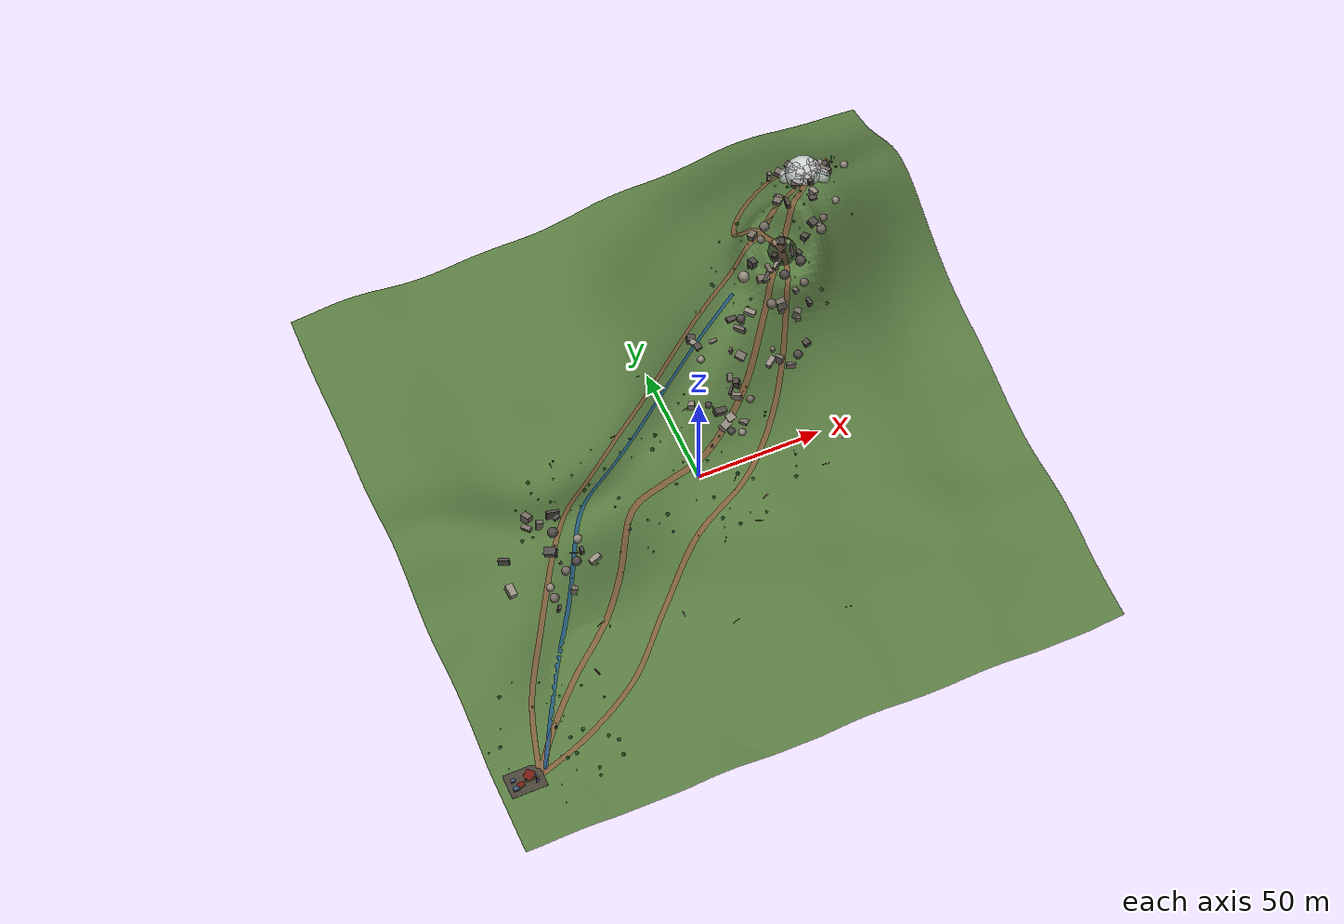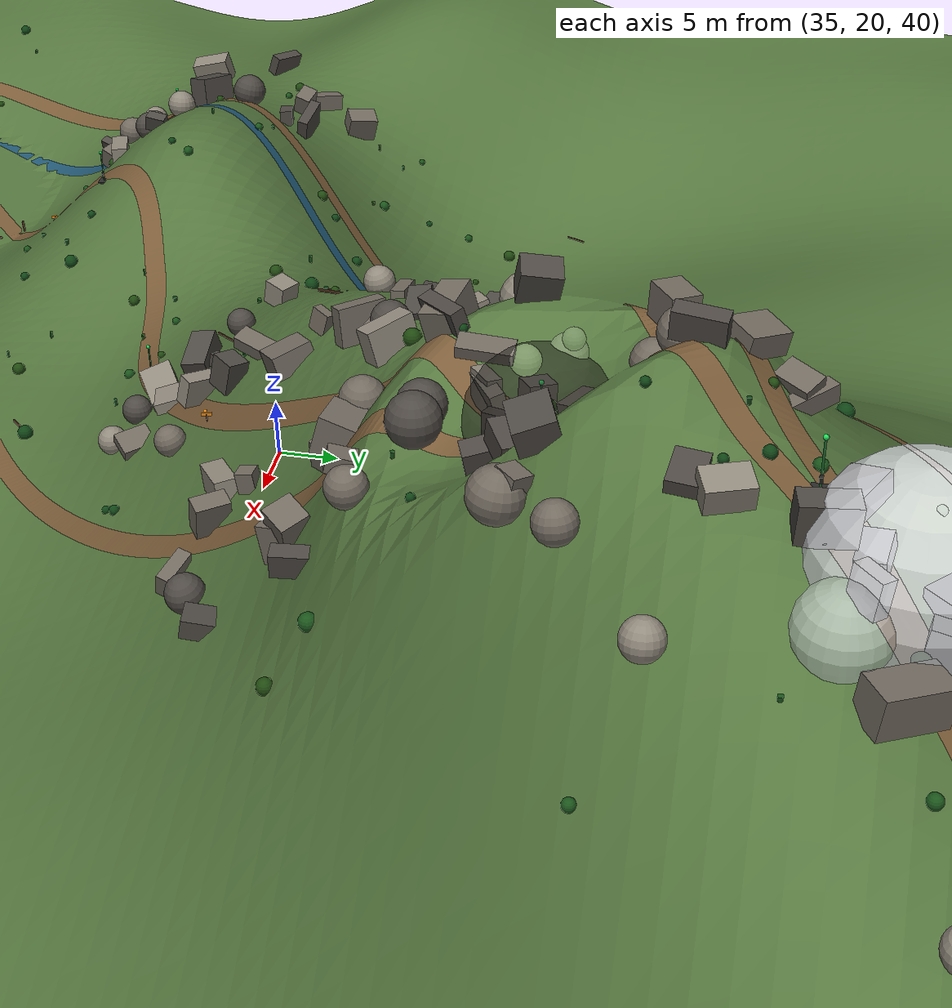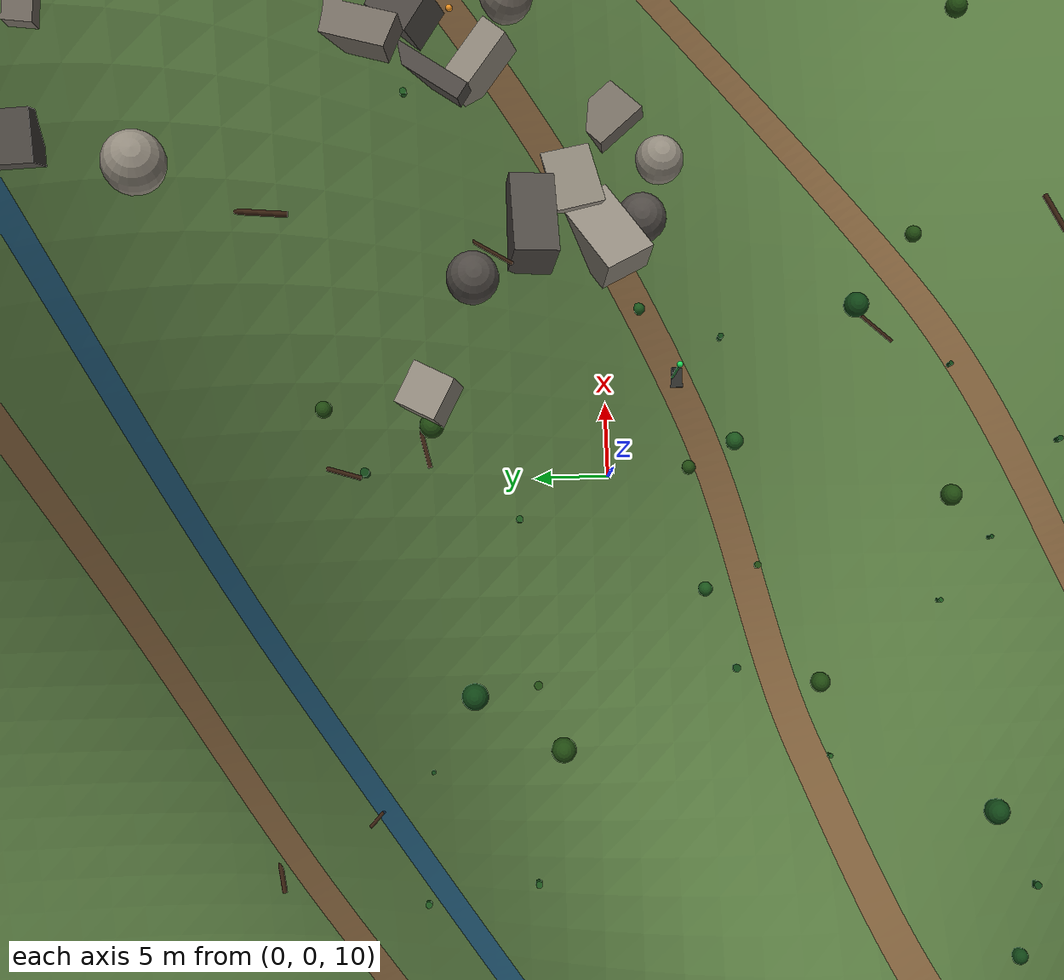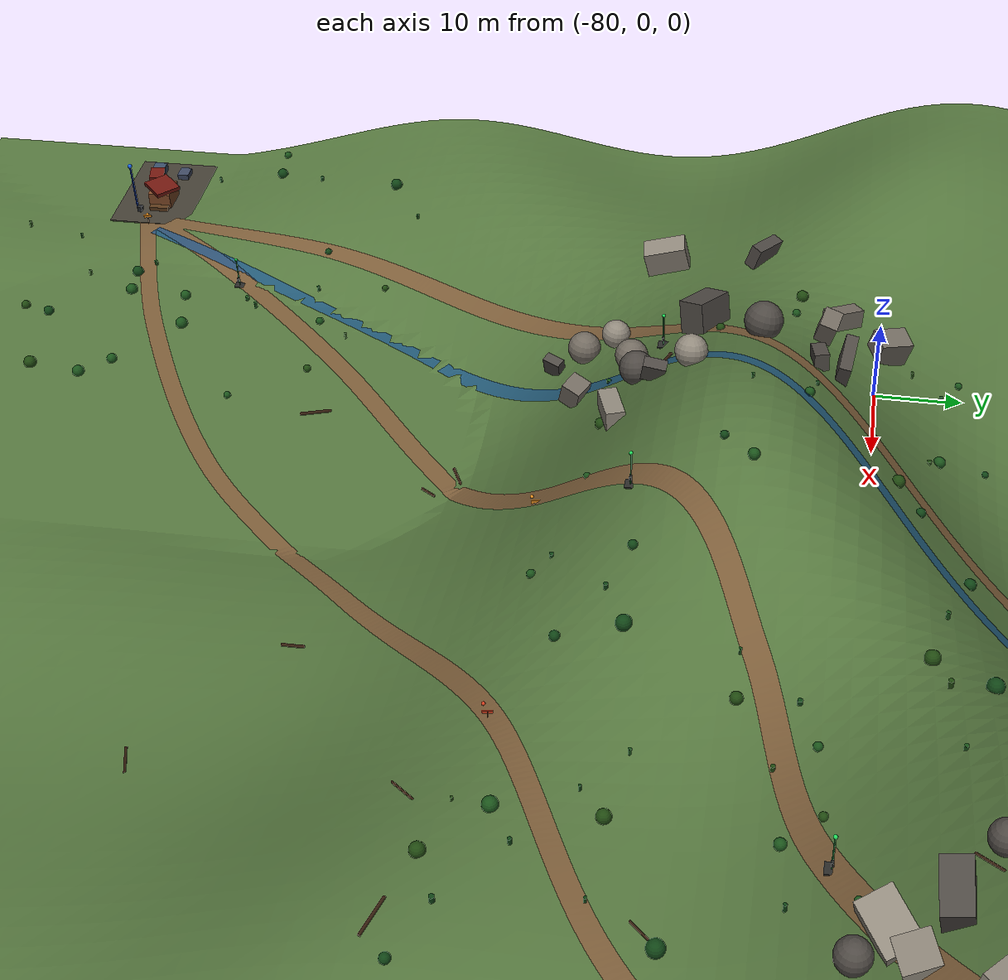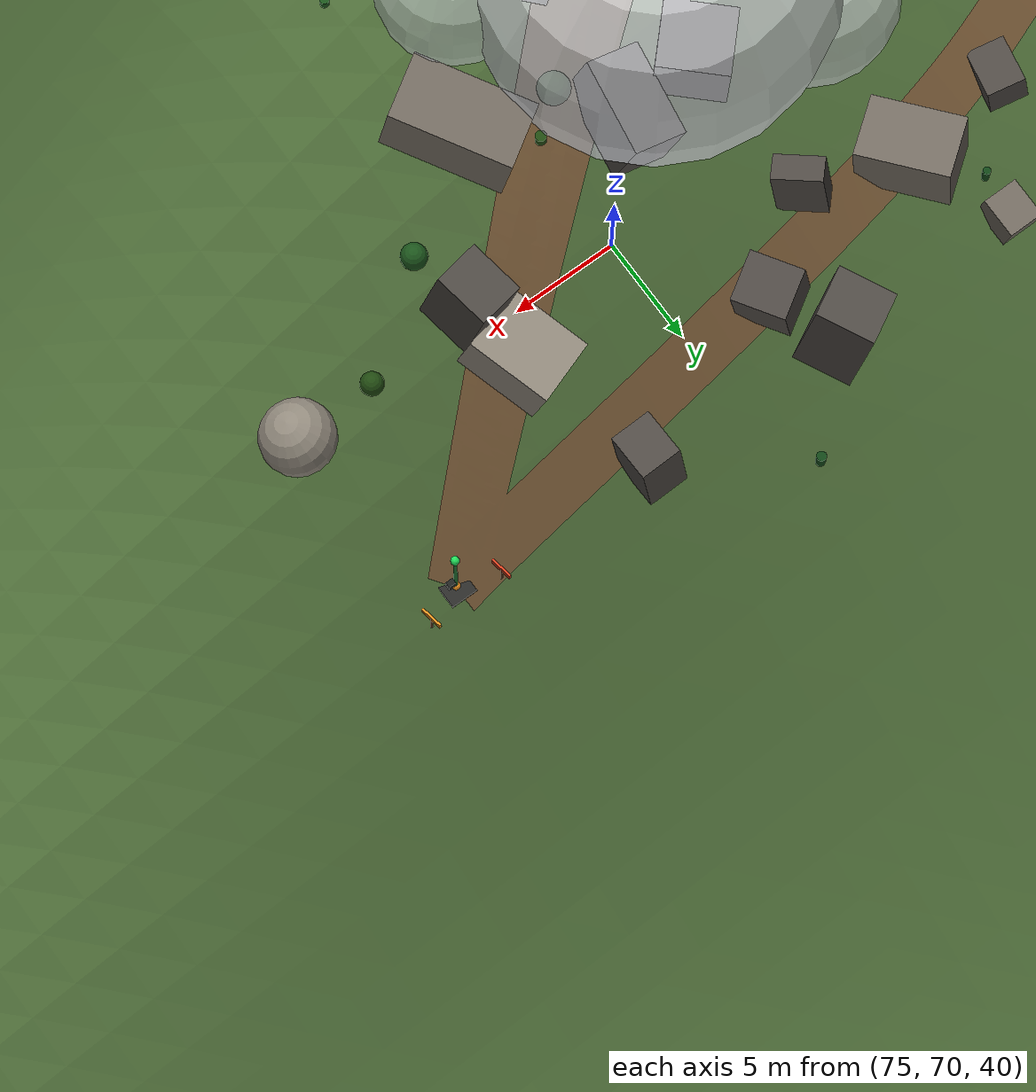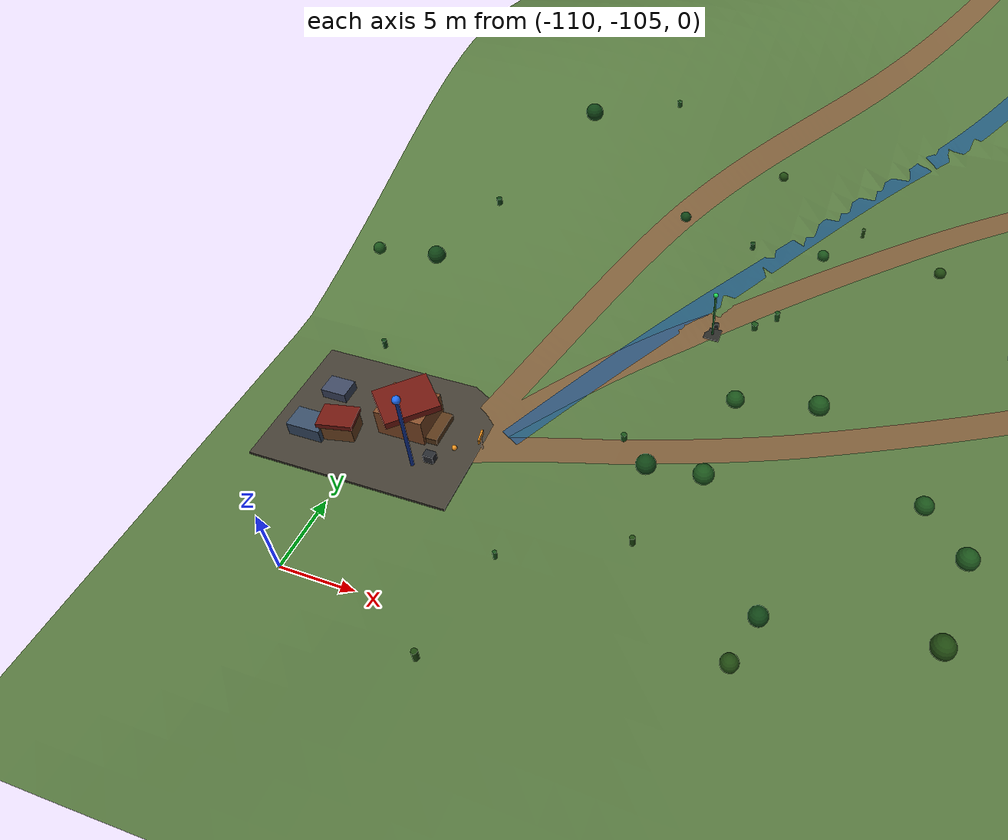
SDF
<sdf version="1.10">
 <world name="hiking_lora_world">
  <plugin filename="gz-sim-physics-system" name="gz::sim::systems::Physics"/>
  <plugin filename="gz-sim-user-commands-system" name="gz::sim::systems::UserCommands"/>
  <plugin filename="gz-sim-scene-broadcaster-system" name="gz::sim::systems::SceneBroadcaster"/>
  <gravity>0 0 -9.81</gravity>
  <magnetic_field>5.5645e-06 2.28758e-05 -4.23884e-05</magnetic_field>
  <atmosphere type="adiabatic"/>
  <scene>
   <ambient>0.42 0.46 0.48 1</ambient>
   <background>0.50 0.68 0.88 1</background>
   <grid>false</grid>
   <fog>
    <type>linear</type>
    <color>0.58 0.67 0.74 1</color>
    <density>0.0007</density>
    <start>120</start>
    <end>360</end>
   </fog>
  </scene>
  <light name="sun" type="directional">
   <pose>0 0 200 0 0 0</pose>
   <intensity>1.05</intensity>
   <direction>-0.38 0.28 -0.88</direction>
   <diffuse>0.95 0.90 0.78 1</diffuse>
   <specular>0.20 0.18 0.15 1</specular>
  </light>
  <light name="sky_fill" type="directional">
   <pose>0 0 150 0 0 0</pose>
   <cast_shadows>false</cast_shadows>
   <intensity>0.38</intensity>
   <direction>0.30 -0.40 -0.87</direction>
   <diffuse>0.58 0.68 0.85 1</diffuse>
   <specular>0.04 0.05 0.06 1</specular>
  </light>
  <model name="wide_mountain_terrain">
   <static>true</static>
   <link name="terrain_link">
    <collision name="terrain_collision">
     <geometry><mesh><uri>model://hiking_lora_terrain/meshes/mountain_terrain.dae</uri></mesh></geometry>
    </collision>
    <visual name="terrain_visual">
     <geometry><mesh><uri>model://hiking_lora_terrain/meshes/mountain_terrain.dae</uri></mesh></geometry>
     <material>
      <ambient>0.22 0.32 0.17 1</ambient>
      <diffuse>0.33 0.46 0.24 1</diffuse>
      <specular>0.06 0.07 0.05 1</specular>
     </material>
    </visual>
    <visual name="trail_surface_visual">
     <geometry><mesh><uri>model://hiking_lora_terrain/meshes/trail_surface.dae</uri></mesh></geometry>
     <material>
      <ambient>0.31 0.22 0.13 1</ambient>
      <diffuse>0.48 0.36 0.22 1</diffuse>
      <specular>0.04 0.03 0.02 1</specular>
     </material>
    </visual>
    <visual name="stream_surface_visual">
     <geometry><mesh><uri>model://hiking_lora_terrain/meshes/stream_surface.dae</uri></mesh></geometry>
     <material>
      <ambient>0.05 0.18 0.32 0.72</ambient>
      <diffuse>0.10 0.34 0.58 0.72</diffuse>
      <specular>0.02 0.04 0.06 1</specular>
     </material>
    </visual>
   </link>
  </model>
  <model name="trail_signs_and_markers">
   <static>true</static>
   <link name="signs">
    <visual name="sign_post_0">
     <pose>-102.35 -93.3 1 0 0 0</pose>
     <geometry><cylinder><radius>0.055</radius><length>1.3</length></cylinder></geometry>
     <material><ambient>0.189 0.11199999999999999 0.049 1</ambient><diffuse>0.27 0.16 0.07 1</diffuse></material>
    </visual>
    <visual name="sign_board_0">
     <pose>-102.35 -93.3 1.63 0 0 0.18</pose>
     <geometry><box><size>0.10 0.95 0.36</size></box></geometry>
     <material>
      <ambient>0.6649999999999999 0.40599999999999997 0.08399999999999999 1</ambient>
      <diffuse>0.95 0.58 0.12 1</diffuse>
     </material>
    </visual>
    <visual name="marker_dot_0">
     <pose>-104 -94 0.71 0 0 0</pose>
     <geometry><sphere><radius>0.18</radius></sphere></geometry>
     <material>
      <ambient>0.6649999999999999 0.40599999999999997 0.08399999999999999 1</ambient>
      <diffuse>0.95 0.58 0.12 1</diffuse>
     </material>
    </visual>
    <visual name="sign_post_1">
     <pose>-45.35 -33.3 10.7071 0 0 0</pose>
     <geometry><cylinder><radius>0.055</radius><length>1.3</length></cylinder></geometry>
     <material><ambient>0.189 0.11199999999999999 0.049 1</ambient><diffuse>0.27 0.16 0.07 1</diffuse></material>
    </visual>
    <visual name="sign_board_1">
     <pose>-45.35 -33.3 11.3371 0 0 0.18</pose>
     <geometry><box><size>0.10 0.95 0.36</size></box></geometry>
     <material>
      <ambient>0.6649999999999999 0.40599999999999997 0.08399999999999999 1</ambient>
      <diffuse>0.95 0.58 0.12 1</diffuse>
     </material>
    </visual>
    <visual name="marker_dot_1">
     <pose>-47 -34 10.4171 0 0 0</pose>
     <geometry><sphere><radius>0.18</radius></sphere></geometry>
     <material>
      <ambient>0.6649999999999999 0.40599999999999997 0.08399999999999999 1</ambient>
      <diffuse>0.95 0.58 0.12 1</diffuse>
     </material>
    </visual>
    <visual name="sign_post_2">
     <pose>23.65 9.7 34.031 0 0 0</pose>
     <geometry><cylinder><radius>0.055</radius><length>1.3</length></cylinder></geometry>
     <material><ambient>0.189 0.11199999999999999 0.049 1</ambient><diffuse>0.27 0.16 0.07 1</diffuse></material>
    </visual>
    <visual name="sign_board_2">
     <pose>23.65 9.7 34.661 0 0 0.18</pose>
     <geometry><box><size>0.10 0.95 0.36</size></box></geometry>
     <material>
      <ambient>0.6649999999999999 0.40599999999999997 0.08399999999999999 1</ambient>
      <diffuse>0.95 0.58 0.12 1</diffuse>
     </material>
    </visual>
    <visual name="marker_dot_2">
     <pose>22 9 33.741 0 0 0</pose>
     <geometry><sphere><radius>0.18</radius></sphere></geometry>
     <material>
      <ambient>0.6649999999999999 0.40599999999999997 0.08399999999999999 1</ambient>
      <diffuse>0.95 0.58 0.12 1</diffuse>
     </material>
    </visual>
    <visual name="sign_post_3">
     <pose>92.65 81.7 52.6138 0 0 0</pose>
     <geometry><cylinder><radius>0.055</radius><length>1.3</length></cylinder></geometry>
     <material><ambient>0.189 0.11199999999999999 0.049 1</ambient><diffuse>0.27 0.16 0.07 1</diffuse></material>
    </visual>
    <visual name="sign_board_3">
     <pose>92.65 81.7 53.2438 0 0 0.18</pose>
     <geometry><box><size>0.10 0.95 0.36</size></box></geometry>
     <material>
      <ambient>0.6649999999999999 0.40599999999999997 0.08399999999999999 1</ambient>
      <diffuse>0.95 0.58 0.12 1</diffuse>
     </material>
    </visual>
    <visual name="marker_dot_3">
     <pose>91 81 52.3238 0 0 0</pose>
     <geometry><sphere><radius>0.18</radius></sphere></geometry>
     <material>
      <ambient>0.6649999999999999 0.40599999999999997 0.08399999999999999 1</ambient>
      <diffuse>0.95 0.58 0.12 1</diffuse>
     </material>
    </visual>
    <visual name="sign_post_4">
     <pose>-102.35 -93.3 1 0 0 0</pose>
     <geometry><cylinder><radius>0.055</radius><length>1.3</length></cylinder></geometry>
     <material><ambient>0.189 0.11199999999999999 0.049 1</ambient><diffuse>0.27 0.16 0.07 1</diffuse></material>
    </visual>
    <visual name="sign_board_4">
     <pose>-102.35 -93.3 1.63 0 0 0.18</pose>
     <geometry><box><size>0.10 0.95 0.36</size></box></geometry>
     <material><ambient>0.21 0.48999999999999994 0.154 1</ambient><diffuse>0.30 0.70 0.22 1</diffuse></material>
    </visual>
    <visual name="marker_dot_4">
     <pose>-104 -94 0.71 0 0 0</pose>
     <geometry><sphere><radius>0.18</radius></sphere></geometry>
     <material><ambient>0.21 0.48999999999999994 0.154 1</ambient><diffuse>0.30 0.70 0.22 1</diffuse></material>
    </visual>
    <visual name="sign_post_5">
     <pose>-69.65 -19.3 17.6076 0 0 0</pose>
     <geometry><cylinder><radius>0.055</radius><length>1.3</length></cylinder></geometry>
     <material><ambient>0.189 0.11199999999999999 0.049 1</ambient><diffuse>0.27 0.16 0.07 1</diffuse></material>
    </visual>
    <visual name="sign_board_5">
     <pose>-69.65 -19.3 18.2376 0 0 0.18</pose>
     <geometry><box><size>0.10 0.95 0.36</size></box></geometry>
     <material><ambient>0.21 0.48999999999999994 0.154 1</ambient><diffuse>0.30 0.70 0.22 1</diffuse></material>
    </visual>
    <visual name="marker_dot_5">
     <pose>-68 -20 17.3176 0 0 0</pose>
     <geometry><sphere><radius>0.18</radius></sphere></geometry>
     <material><ambient>0.21 0.48999999999999994 0.154 1</ambient><diffuse>0.30 0.70 0.22 1</diffuse></material>
    </visual>
    <visual name="sign_post_6">
     <pose>17.35 42.7 43.7753 0 0 0</pose>
     <geometry><cylinder><radius>0.055</radius><length>1.3</length></cylinder></geometry>
     <material><ambient>0.189 0.11199999999999999 0.049 1</ambient><diffuse>0.27 0.16 0.07 1</diffuse></material>
    </visual>
    <visual name="sign_board_6">
     <pose>17.35 42.7 44.4053 0 0 0.18</pose>
     <geometry><box><size>0.10 0.95 0.36</size></box></geometry>
     <material><ambient>0.21 0.48999999999999994 0.154 1</ambient><diffuse>0.30 0.70 0.22 1</diffuse></material>
    </visual>
    <visual name="marker_dot_6">
     <pose>19 42 43.4853 0 0 0</pose>
     <geometry><sphere><radius>0.18</radius></sphere></geometry>
     <material><ambient>0.21 0.48999999999999994 0.154 1</ambient><diffuse>0.30 0.70 0.22 1</diffuse></material>
    </visual>
    <visual name="sign_post_7">
     <pose>92.65 81.7 52.6138 0 0 0</pose>
     <geometry><cylinder><radius>0.055</radius><length>1.3</length></cylinder></geometry>
     <material><ambient>0.189 0.11199999999999999 0.049 1</ambient><diffuse>0.27 0.16 0.07 1</diffuse></material>
    </visual>
    <visual name="sign_board_7">
     <pose>92.65 81.7 53.2438 0 0 0.18</pose>
     <geometry><box><size>0.10 0.95 0.36</size></box></geometry>
     <material><ambient>0.21 0.48999999999999994 0.154 1</ambient><diffuse>0.30 0.70 0.22 1</diffuse></material>
    </visual>
    <visual name="marker_dot_7">
     <pose>91 81 52.3238 0 0 0</pose>
     <geometry><sphere><radius>0.18</radius></sphere></geometry>
     <material><ambient>0.21 0.48999999999999994 0.154 1</ambient><diffuse>0.30 0.70 0.22 1</diffuse></material>
    </visual>
    <visual name="sign_post_8">
     <pose>-102.35 -93.3 1 0 0 0</pose>
     <geometry><cylinder><radius>0.055</radius><length>1.3</length></cylinder></geometry>
     <material><ambient>0.189 0.11199999999999999 0.049 1</ambient><diffuse>0.27 0.16 0.07 1</diffuse></material>
    </visual>
    <visual name="sign_board_8">
     <pose>-102.35 -93.3 1.63 0 0 0.18</pose>
     <geometry><box><size>0.10 0.95 0.36</size></box></geometry>
     <material><ambient>0.595 0.175 0.08399999999999999 1</ambient><diffuse>0.85 0.25 0.12 1</diffuse></material>
    </visual>
    <visual name="marker_dot_8">
     <pose>-104 -94 0.71 0 0 0</pose>
     <geometry><sphere><radius>0.18</radius></sphere></geometry>
     <material><ambient>0.595 0.175 0.08399999999999999 1</ambient><diffuse>0.85 0.25 0.12 1</diffuse></material>
    </visual>
    <visual name="sign_post_9">
     <pose>-14.35 -32.3 15.0384 0 0 0</pose>
     <geometry><cylinder><radius>0.055</radius><length>1.3</length></cylinder></geometry>
     <material><ambient>0.189 0.11199999999999999 0.049 1</ambient><diffuse>0.27 0.16 0.07 1</diffuse></material>
    </visual>
    <visual name="sign_board_9">
     <pose>-14.35 -32.3 15.6684 0 0 0.18</pose>
     <geometry><box><size>0.10 0.95 0.36</size></box></geometry>
     <material><ambient>0.595 0.175 0.08399999999999999 1</ambient><diffuse>0.85 0.25 0.12 1</diffuse></material>
    </visual>
    <visual name="marker_dot_9">
     <pose>-16 -33 14.7484 0 0 0</pose>
     <geometry><sphere><radius>0.18</radius></sphere></geometry>
     <material><ambient>0.595 0.175 0.08399999999999999 1</ambient><diffuse>0.85 0.25 0.12 1</diffuse></material>
    </visual>
    <visual name="sign_post_10">
     <pose>55.65 45.7 59.8318 0 0 0</pose>
     <geometry><cylinder><radius>0.055</radius><length>1.3</length></cylinder></geometry>
     <material><ambient>0.189 0.11199999999999999 0.049 1</ambient><diffuse>0.27 0.16 0.07 1</diffuse></material>
    </visual>
    <visual name="sign_board_10">
     <pose>55.65 45.7 60.4618 0 0 0.18</pose>
     <geometry><box><size>0.10 0.95 0.36</size></box></geometry>
     <material><ambient>0.595 0.175 0.08399999999999999 1</ambient><diffuse>0.85 0.25 0.12 1</diffuse></material>
    </visual>
    <visual name="marker_dot_10">
     <pose>54 45 59.5418 0 0 0</pose>
     <geometry><sphere><radius>0.18</radius></sphere></geometry>
     <material><ambient>0.595 0.175 0.08399999999999999 1</ambient><diffuse>0.85 0.25 0.12 1</diffuse></material>
    </visual>
    <visual name="sign_post_11">
     <pose>89.35 81.7 52.6138 0 0 0</pose>
     <geometry><cylinder><radius>0.055</radius><length>1.3</length></cylinder></geometry>
     <material><ambient>0.189 0.11199999999999999 0.049 1</ambient><diffuse>0.27 0.16 0.07 1</diffuse></material>
    </visual>
    <visual name="sign_board_11">
     <pose>89.35 81.7 53.2438 0 0 0.18</pose>
     <geometry><box><size>0.10 0.95 0.36</size></box></geometry>
     <material><ambient>0.595 0.175 0.08399999999999999 1</ambient><diffuse>0.85 0.25 0.12 1</diffuse></material>
    </visual>
    <visual name="marker_dot_11">
     <pose>91 81 52.3238 0 0 0</pose>
     <geometry><sphere><radius>0.18</radius></sphere></geometry>
     <material><ambient>0.595 0.175 0.08399999999999999 1</ambient><diffuse>0.85 0.25 0.12 1</diffuse></material>
    </visual>
   </link>
  </model>
  <model name="base_camp">
   <static>true</static>
   <pose>-109.5 -93.5 0 0 0 0</pose>
   <link name="camp_link">
    <visual name="platform">
     <pose>0 0 0.44 0 0 0</pose>
     <geometry><box><size>14.0 10.0 0.18</size></box></geometry>
     <material>
      <ambient>0.182 0.16799999999999998 0.13999999999999999 1</ambient>
      <diffuse>0.26 0.24 0.20 1</diffuse>
     </material>
    </visual>
    <visual name="hut_main">
     <pose>1.8 0.6 1.45 0 0 0</pose>
     <geometry><box><size>3.4 2.8 2.2</size></box></geometry>
     <material><ambient>0.364 0.21 0.11199999999999999 1</ambient><diffuse>0.52 0.30 0.16 1</diffuse></material>
    </visual>
    <visual name="roof">
     <pose>1.8 0.6 2.77 0 0 0.785</pose>
     <geometry><box><size>3.7 3.2 0.48</size></box></geometry>
     <material><ambient>0.308 0.063 0.041999999999999996 1</ambient><diffuse>0.44 0.09 0.06 1</diffuse></material>
    </visual>
    <visual name="hut_small">
     <pose>-2.2 -1.5 1.1 0 0 0.2</pose>
     <geometry><box><size>2.2 1.6 1.5</size></box></geometry>
     <material><ambient>0.322 0.196 0.098 1</ambient><diffuse>0.46 0.28 0.14 1</diffuse></material>
    </visual>
    <visual name="roof_small">
     <pose>-2.2 -1.5 1.93 0 0 0.2</pose>
     <geometry><box><size>2.4 1.8 0.35</size></box></geometry>
     <material><ambient>0.308 0.063 0.041999999999999996 1</ambient><diffuse>0.44 0.09 0.06 1</diffuse></material>
    </visual>
    <visual name="equipment_a">
     <pose>-4.2 -2.0 0.95 0 0 0</pose>
     <geometry><box><size>2.4 1.6 1.2</size></box></geometry>
     <material><ambient>0.154 0.21 0.27999999999999997 1</ambient><diffuse>0.22 0.30 0.40 1</diffuse></material>
    </visual>
    <visual name="equipment_b">
     <pose>-4.2 1.5 0.8 0 0 0</pose>
     <geometry><box><size>1.8 1.4 0.9</size></box></geometry>
     <material>
      <ambient>0.16799999999999998 0.196 0.26599999999999996 1</ambient>
      <diffuse>0.24 0.28 0.38 1</diffuse>
     </material>
    </visual>
    <visual name="bench">
     <pose>3.8 0.6 0.81 0 0 0</pose>
     <geometry><box><size>1.0 2.4 0.5</size></box></geometry>
     <material>
      <ambient>0.24499999999999997 0.154 0.06999999999999999 1</ambient>
      <diffuse>0.35 0.22 0.10 1</diffuse>
     </material>
    </visual>
   </link>
  </model>
  <model name="base_station">
   <static>true</static>
   <pose>-106 -96 0 0 0 0</pose>
   <link name="tower">
    <visual name="foundation">
     <pose>0 0 0.43 0 0 0</pose>
     <geometry><box><size>2.4 2.4 0.16</size></box></geometry>
     <material>
      <ambient>0.11199999999999999 0.11199999999999999 0.105 1</ambient>
      <diffuse>0.16 0.16 0.15 1</diffuse>
     </material>
    </visual>
    <visual name="mast">
     <pose>0 0 3.51 0 0 0</pose>
     <geometry><cylinder><radius>0.12</radius><length>6</length></cylinder></geometry>
     <material><ambient>0.034999999999999996 0.126 0.385 1</ambient><diffuse>0.05 0.18 0.55 1</diffuse></material>
    </visual>
    <visual name="antenna">
     <pose>0 0 6.63 0 0 0</pose>
     <geometry><sphere><radius>0.28</radius></sphere></geometry>
     <material>
      <ambient>0.08399999999999999 0.294 0.6649999999999999 1</ambient>
      <diffuse>0.12 0.42 0.95 1</diffuse>
     </material>
    </visual>
    <visual name="shelter">
     <pose>0.92 0.70 0.81 0 0 0</pose>
     <geometry><box><size>0.70 0.55 0.76</size></box></geometry>
     <material><ambient>0.105 0.11199999999999999 0.126 1</ambient><diffuse>0.15 0.16 0.18 1</diffuse></material>
    </visual>
   </link>
  </model>
  <model name="node_basecamp_gate">
   <static>true</static>
   <pose>-91 -78 0 0 0 0</pose>
   <link name="tower">
    <visual name="foundation">
     <pose>0 0 0.43 0 0 0</pose>
     <geometry><box><size>1.15 1.15 0.16</size></box></geometry>
     <material>
      <ambient>0.11199999999999999 0.11199999999999999 0.105 1</ambient>
      <diffuse>0.16 0.16 0.15 1</diffuse>
     </material>
    </visual>
    <visual name="mast">
     <pose>0 0 2.31 0 0 0</pose>
     <geometry><cylinder><radius>0.075</radius><length>3.6</length></cylinder></geometry>
     <material><ambient>0.08399999999999999 0.294 0.126 1</ambient><diffuse>0.12 0.42 0.18 1</diffuse></material>
    </visual>
    <visual name="antenna">
     <pose>0 0 4.23 0 0 0</pose>
     <geometry><sphere><radius>0.18</radius></sphere></geometry>
     <material><ambient>0.08399999999999999 0.595 0.238 1</ambient><diffuse>0.12 0.85 0.34 1</diffuse></material>
    </visual>
    <visual name="relay_box">
     <pose>0.24 0.0 1.4 0 0 0</pose>
     <geometry><box><size>0.32 0.24 0.42</size></box></geometry>
     <material>
      <ambient>0.08399999999999999 0.091 0.08399999999999999 1</ambient>
      <diffuse>0.12 0.13 0.12 1</diffuse>
     </material>
    </visual>
   </link>
  </model>
  <model name="node_valley_watch">
   <static>true</static>
   <pose>-66 -23 0 0 0 0</pose>
   <link name="tower">
    <visual name="foundation">
     <pose>0 0 16.0094 0 0 0</pose>
     <geometry><box><size>1.15 1.15 0.16</size></box></geometry>
     <material>
      <ambient>0.11199999999999999 0.11199999999999999 0.105 1</ambient>
      <diffuse>0.16 0.16 0.15 1</diffuse>
     </material>
    </visual>
    <visual name="mast">
     <pose>0 0 17.8894 0 0 0</pose>
     <geometry><cylinder><radius>0.075</radius><length>3.6</length></cylinder></geometry>
     <material><ambient>0.08399999999999999 0.294 0.126 1</ambient><diffuse>0.12 0.42 0.18 1</diffuse></material>
    </visual>
    <visual name="antenna">
     <pose>0 0 19.8094 0 0 0</pose>
     <geometry><sphere><radius>0.18</radius></sphere></geometry>
     <material><ambient>0.08399999999999999 0.595 0.238 1</ambient><diffuse>0.12 0.85 0.34 1</diffuse></material>
    </visual>
    <visual name="relay_box">
     <pose>0.24 0.0 16.9794 0 0 0</pose>
     <geometry><box><size>0.32 0.24 0.42</size></box></geometry>
     <material>
      <ambient>0.08399999999999999 0.091 0.08399999999999999 1</ambient>
      <diffuse>0.12 0.13 0.12 1</diffuse>
     </material>
    </visual>
   </link>
  </model>
  <model name="node_forest_pass">
   <static>true</static>
   <pose>-38 -23 0 0 0 0</pose>
   <link name="tower">
    <visual name="foundation">
     <pose>0 0 21.5243 0 0 0</pose>
     <geometry><box><size>1.15 1.15 0.16</size></box></geometry>
     <material>
      <ambient>0.11199999999999999 0.11199999999999999 0.105 1</ambient>
      <diffuse>0.16 0.16 0.15 1</diffuse>
     </material>
    </visual>
    <visual name="mast">
     <pose>0 0 23.4043 0 0 0</pose>
     <geometry><cylinder><radius>0.075</radius><length>3.6</length></cylinder></geometry>
     <material><ambient>0.08399999999999999 0.294 0.126 1</ambient><diffuse>0.12 0.42 0.18 1</diffuse></material>
    </visual>
    <visual name="antenna">
     <pose>0 0 25.3243 0 0 0</pose>
     <geometry><sphere><radius>0.18</radius></sphere></geometry>
     <material><ambient>0.08399999999999999 0.595 0.238 1</ambient><diffuse>0.12 0.85 0.34 1</diffuse></material>
    </visual>
    <visual name="relay_box">
     <pose>0.24 0.0 22.4943 0 0 0</pose>
     <geometry><box><size>0.32 0.24 0.42</size></box></geometry>
     <material>
      <ambient>0.08399999999999999 0.091 0.08399999999999999 1</ambient>
      <diffuse>0.12 0.13 0.12 1</diffuse>
     </material>
    </visual>
   </link>
  </model>
  <model name="node_ridge_mid">
   <static>true</static>
   <pose>4 -3 0 0 0 0</pose>
   <link name="tower">
    <visual name="foundation">
     <pose>0 0 23.7151 0 0 0</pose>
     <geometry><box><size>1.15 1.15 0.16</size></box></geometry>
     <material>
      <ambient>0.11199999999999999 0.11199999999999999 0.105 1</ambient>
      <diffuse>0.16 0.16 0.15 1</diffuse>
     </material>
    </visual>
    <visual name="mast">
     <pose>0 0 25.5951 0 0 0</pose>
     <geometry><cylinder><radius>0.075</radius><length>3.6</length></cylinder></geometry>
     <material><ambient>0.08399999999999999 0.294 0.126 1</ambient><diffuse>0.12 0.42 0.18 1</diffuse></material>
    </visual>
    <visual name="antenna">
     <pose>0 0 27.5151 0 0 0</pose>
     <geometry><sphere><radius>0.18</radius></sphere></geometry>
     <material><ambient>0.08399999999999999 0.595 0.238 1</ambient><diffuse>0.12 0.85 0.34 1</diffuse></material>
    </visual>
    <visual name="relay_box">
     <pose>0.24 0.0 24.6851 0 0 0</pose>
     <geometry><box><size>0.32 0.24 0.42</size></box></geometry>
     <material>
      <ambient>0.08399999999999999 0.091 0.08399999999999999 1</ambient>
      <diffuse>0.12 0.13 0.12 1</diffuse>
     </material>
    </visual>
   </link>
  </model>
  <model name="node_crater_edge">
   <static>true</static>
   <pose>54 45 0 0 0 0</pose>
   <link name="tower">
    <visual name="foundation">
     <pose>0 0 59.2618 0 0 0</pose>
     <geometry><box><size>1.15 1.15 0.16</size></box></geometry>
     <material>
      <ambient>0.11199999999999999 0.11199999999999999 0.105 1</ambient>
      <diffuse>0.16 0.16 0.15 1</diffuse>
     </material>
    </visual>
    <visual name="mast">
     <pose>0 0 61.1418 0 0 0</pose>
     <geometry><cylinder><radius>0.075</radius><length>3.6</length></cylinder></geometry>
     <material><ambient>0.08399999999999999 0.294 0.126 1</ambient><diffuse>0.12 0.42 0.18 1</diffuse></material>
    </visual>
    <visual name="antenna">
     <pose>0 0 63.0618 0 0 0</pose>
     <geometry><sphere><radius>0.18</radius></sphere></geometry>
     <material><ambient>0.08399999999999999 0.595 0.238 1</ambient><diffuse>0.12 0.85 0.34 1</diffuse></material>
    </visual>
    <visual name="relay_box">
     <pose>0.24 0.0 60.2318 0 0 0</pose>
     <geometry><box><size>0.32 0.24 0.42</size></box></geometry>
     <material>
      <ambient>0.08399999999999999 0.091 0.08399999999999999 1</ambient>
      <diffuse>0.12 0.13 0.12 1</diffuse>
     </material>
    </visual>
   </link>
  </model>
  <model name="node_north_saddle">
   <static>true</static>
   <pose>70 64 0 0 0 0</pose>
   <link name="tower">
    <visual name="foundation">
     <pose>0 0 68.7087 0 0 0</pose>
     <geometry><box><size>1.15 1.15 0.16</size></box></geometry>
     <material>
      <ambient>0.11199999999999999 0.11199999999999999 0.105 1</ambient>
      <diffuse>0.16 0.16 0.15 1</diffuse>
     </material>
    </visual>
    <visual name="mast">
     <pose>0 0 70.5887 0 0 0</pose>
     <geometry><cylinder><radius>0.075</radius><length>3.6</length></cylinder></geometry>
     <material><ambient>0.08399999999999999 0.294 0.126 1</ambient><diffuse>0.12 0.42 0.18 1</diffuse></material>
    </visual>
    <visual name="antenna">
     <pose>0 0 72.5087 0 0 0</pose>
     <geometry><sphere><radius>0.18</radius></sphere></geometry>
     <material><ambient>0.08399999999999999 0.595 0.238 1</ambient><diffuse>0.12 0.85 0.34 1</diffuse></material>
    </visual>
    <visual name="relay_box">
     <pose>0.24 0.0 69.6787 0 0 0</pose>
     <geometry><box><size>0.32 0.24 0.42</size></box></geometry>
     <material>
      <ambient>0.08399999999999999 0.091 0.08399999999999999 1</ambient>
      <diffuse>0.12 0.13 0.12 1</diffuse>
     </material>
    </visual>
   </link>
  </model>
  <model name="node_summit_view">
   <static>true</static>
   <pose>91 81 0 0 0 0</pose>
   <link name="tower">
    <visual name="foundation">
     <pose>0 0 52.0438 0 0 0</pose>
     <geometry><box><size>1.15 1.15 0.16</size></box></geometry>
     <material>
      <ambient>0.11199999999999999 0.11199999999999999 0.105 1</ambient>
      <diffuse>0.16 0.16 0.15 1</diffuse>
     </material>
    </visual>
    <visual name="mast">
     <pose>0 0 53.9238 0 0 0</pose>
     <geometry><cylinder><radius>0.075</radius><length>3.6</length></cylinder></geometry>
     <material><ambient>0.08399999999999999 0.294 0.126 1</ambient><diffuse>0.12 0.42 0.18 1</diffuse></material>
    </visual>
    <visual name="antenna">
     <pose>0 0 55.8438 0 0 0</pose>
     <geometry><sphere><radius>0.18</radius></sphere></geometry>
     <material><ambient>0.08399999999999999 0.595 0.238 1</ambient><diffuse>0.12 0.85 0.34 1</diffuse></material>
    </visual>
    <visual name="relay_box">
     <pose>0.24 0.0 53.0138 0 0 0</pose>
     <geometry><box><size>0.32 0.24 0.42</size></box></geometry>
     <material>
      <ambient>0.08399999999999999 0.091 0.08399999999999999 1</ambient>
      <diffuse>0.12 0.13 0.12 1</diffuse>
     </material>
    </visual>
   </link>
  </model>
  <model name="low_ground_cover">
   <static>true</static>
   <link name="cover">
    <visual name="grass_0">
     <pose>-113.0764 -86.8746 0.706 0 0 0</pose>
     <geometry><cylinder><radius>0.1638</radius><length>0.7911</length></cylinder></geometry>
     <material>
      <ambient>0.041999999999999996 0.182 0.055999999999999994 1</ambient>
      <diffuse>0.06 0.26 0.08 1</diffuse>
     </material>
    </visual>
    <visual name="shrub_1">
     <pose>-74.7001 -88.7608 0.6074 0 0 0</pose>
     <geometry><sphere><radius>0.6128</radius></sphere></geometry>
     <material>
      <ambient>0.06999999999999999 0.22399999999999998 0.06999999999999999 1</ambient>
      <diffuse>0.10 0.32 0.10 1</diffuse>
     </material>
    </visual>
    <visual name="shrub_2">
     <pose>-88.1718 -90.81 0.6437 0 0 0</pose>
     <geometry><sphere><radius>0.6994</radius></sphere></geometry>
     <material>
      <ambient>0.06999999999999999 0.22399999999999998 0.06999999999999999 1</ambient>
      <diffuse>0.10 0.32 0.10 1</diffuse>
     </material>
    </visual>
    <visual name="shrub_3">
     <pose>-91.8624 -91.2293 0.6368 0 0 0</pose>
     <geometry><sphere><radius>0.6829</radius></sphere></geometry>
     <material>
      <ambient>0.041999999999999996 0.182 0.055999999999999994 1</ambient>
      <diffuse>0.06 0.26 0.08 1</diffuse>
     </material>
    </visual>
    <visual name="grass_4">
     <pose>-93.9112 -89.5709 0.64 0 0 0</pose>
     <geometry><cylinder><radius>0.1964</radius><length>0.6444</length></cylinder></geometry>
     <material>
      <ambient>0.06999999999999999 0.22399999999999998 0.06999999999999999 1</ambient>
      <diffuse>0.10 0.32 0.10 1</diffuse>
     </material>
    </visual>
    <visual name="shrub_5">
     <pose>-96.0876 -67.8556 2.7714 0 0 0</pose>
     <geometry><sphere><radius>0.4306</radius></sphere></geometry>
     <material>
      <ambient>0.041999999999999996 0.182 0.055999999999999994 1</ambient>
      <diffuse>0.06 0.26 0.08 1</diffuse>
     </material>
    </visual>
    <visual name="shrub_6">
     <pose>-75.8782 -65.5857 0.544 0 0 0</pose>
     <geometry><sphere><radius>0.4618</radius></sphere></geometry>
     <material>
      <ambient>0.08399999999999999 0.196 0.041999999999999996 1</ambient>
      <diffuse>0.12 0.28 0.06 1</diffuse>
     </material>
    </visual>
    <visual name="shrub_7">
     <pose>-83.5004 -102.5779 0.581 0 0 0</pose>
     <geometry><sphere><radius>0.55</radius></sphere></geometry>
     <material>
      <ambient>0.08399999999999999 0.196 0.041999999999999996 1</ambient>
      <diffuse>0.12 0.28 0.06 1</diffuse>
     </material>
    </visual>
    <visual name="grass_8">
     <pose>-110.3685 -72.125 3.9153 0 0 0</pose>
     <geometry><cylinder><radius>0.2132</radius><length>0.5527</length></cylinder></geometry>
     <material>
      <ambient>0.041999999999999996 0.182 0.055999999999999994 1</ambient>
      <diffuse>0.06 0.26 0.08 1</diffuse>
     </material>
    </visual>
    <visual name="shrub_9">
     <pose>-106.2279 -61.1816 6.6232 0 0 0</pose>
     <geometry><sphere><radius>0.7226</radius></sphere></geometry>
     <material>
      <ambient>0.041999999999999996 0.182 0.055999999999999994 1</ambient>
      <diffuse>0.06 0.26 0.08 1</diffuse>
     </material>
    </visual>
    <visual name="shrub_10">
     <pose>-117.7133 -78.8346 2.2994 0 0 0</pose>
     <geometry><sphere><radius>0.4739</radius></sphere></geometry>
     <material>
      <ambient>0.06999999999999999 0.22399999999999998 0.06999999999999999 1</ambient>
      <diffuse>0.10 0.32 0.10 1</diffuse>
     </material>
    </visual>
    <visual name="grass_11">
     <pose>-90.4567 -67.8402 1.2494 0 0 0</pose>
     <geometry><cylinder><radius>0.1902</radius><length>0.6085</length></cylinder></geometry>
     <material>
      <ambient>0.041999999999999996 0.182 0.055999999999999994 1</ambient>
      <diffuse>0.06 0.26 0.08 1</diffuse>
     </material>
    </visual>
    <visual name="grass_12">
     <pose>-99.9086 -57.1313 6.4118 0 0 0</pose>
     <geometry><cylinder><radius>0.1838</radius><length>0.5047</length></cylinder></geometry>
     <material>
      <ambient>0.06999999999999999 0.22399999999999998 0.06999999999999999 1</ambient>
      <diffuse>0.10 0.32 0.10 1</diffuse>
     </material>
    </visual>
    <visual name="shrub_13">
     <pose>-72.7634 -97.9829 0.6616 0 0 0</pose>
     <geometry><sphere><radius>0.7419</radius></sphere></geometry>
     <material>
      <ambient>0.08399999999999999 0.196 0.041999999999999996 1</ambient>
      <diffuse>0.12 0.28 0.06 1</diffuse>
     </material>
    </visual>
    <visual name="shrub_14">
     <pose>-69.9888 -73.4585 0.5298 0 0 0</pose>
     <geometry><sphere><radius>0.428</radius></sphere></geometry>
     <material>
      <ambient>0.06999999999999999 0.22399999999999998 0.06999999999999999 1</ambient>
      <diffuse>0.10 0.32 0.10 1</diffuse>
     </material>
    </visual>
    <visual name="shrub_15">
     <pose>-84.9399 -66.3833 0.5497 0 0 0</pose>
     <geometry><sphere><radius>0.4754</radius></sphere></geometry>
     <material>
      <ambient>0.06999999999999999 0.22399999999999998 0.06999999999999999 1</ambient>
      <diffuse>0.10 0.32 0.10 1</diffuse>
     </material>
    </visual>
    <visual name="shrub_16">
     <pose>-71.9075 -91.845 0.6458 0 0 0</pose>
     <geometry><sphere><radius>0.7042</radius></sphere></geometry>
     <material>
      <ambient>0.06999999999999999 0.22399999999999998 0.06999999999999999 1</ambient>
      <diffuse>0.10 0.32 0.10 1</diffuse>
     </material>
    </visual>
    <visual name="grass_17">
     <pose>-86.901 -74.8414 0.7006 0 0 0</pose>
     <geometry><cylinder><radius>0.1857</radius><length>0.7791</length></cylinder></geometry>
     <material>
      <ambient>0.06999999999999999 0.22399999999999998 0.06999999999999999 1</ambient>
      <diffuse>0.10 0.32 0.10 1</diffuse>
     </material>
    </visual>
    <visual name="grass_18">
     <pose>-90.8436 -97.0049 0.682 0 0 0</pose>
     <geometry><cylinder><radius>0.1762</radius><length>0.7378</length></cylinder></geometry>
     <material>
      <ambient>0.08399999999999999 0.196 0.041999999999999996 1</ambient>
      <diffuse>0.12 0.28 0.06 1</diffuse>
     </material>
    </visual>
    <visual name="grass_19">
     <pose>-82.3581 -62.5881 0.7299 0 0 0</pose>
     <geometry><cylinder><radius>0.1377</radius><length>0.8443</length></cylinder></geometry>
     <material>
      <ambient>0.08399999999999999 0.196 0.041999999999999996 1</ambient>
      <diffuse>0.12 0.28 0.06 1</diffuse>
     </material>
    </visual>
    <visual name="shrub_20">
     <pose>-113.0512 -78.2675 2.4125 0 0 0</pose>
     <geometry><sphere><radius>0.6883</radius></sphere></geometry>
     <material>
      <ambient>0.041999999999999996 0.182 0.055999999999999994 1</ambient>
      <diffuse>0.06 0.26 0.08 1</diffuse>
     </material>
    </visual>
    <visual name="grass_21">
     <pose>-99.3945 -107.857 1.1773 0 0 0</pose>
     <geometry><cylinder><radius>0.1883</radius><length>0.8369</length></cylinder></geometry>
     <material>
      <ambient>0.08399999999999999 0.196 0.041999999999999996 1</ambient>
      <diffuse>0.12 0.28 0.06 1</diffuse>
     </material>
    </visual>
    <visual name="shrub_22">
     <pose>-87.8278 -83.9045 0.6161 0 0 0</pose>
     <geometry><sphere><radius>0.6335</radius></sphere></geometry>
     <material>
      <ambient>0.06999999999999999 0.22399999999999998 0.06999999999999999 1</ambient>
      <diffuse>0.10 0.32 0.10 1</diffuse>
     </material>
    </visual>
    <visual name="grass_23">
     <pose>-88.2637 -76.2955 0.5764 0 0 0</pose>
     <geometry><cylinder><radius>0.2379</radius><length>0.503</length></cylinder></geometry>
     <material>
      <ambient>0.06999999999999999 0.22399999999999998 0.06999999999999999 1</ambient>
      <diffuse>0.10 0.32 0.10 1</diffuse>
     </material>
    </visual>
    <visual name="shrub_24">
     <pose>-82.6636 -99.3814 0.6066 0 0 0</pose>
     <geometry><sphere><radius>0.6109</radius></sphere></geometry>
     <material>
      <ambient>0.041999999999999996 0.182 0.055999999999999994 1</ambient>
      <diffuse>0.06 0.26 0.08 1</diffuse>
     </material>
    </visual>
    <visual name="grass_25">
     <pose>-98.0834 -100.6363 0.8654 0 0 0</pose>
     <geometry><cylinder><radius>0.1344</radius><length>0.6605</length></cylinder></geometry>
     <material>
      <ambient>0.06999999999999999 0.22399999999999998 0.06999999999999999 1</ambient>
      <diffuse>0.10 0.32 0.10 1</diffuse>
     </material>
    </visual>
    <visual name="shrub_26">
     <pose>-89.8793 -59.3099 2.5058 0 0 0</pose>
     <geometry><sphere><radius>0.3993</radius></sphere></geometry>
     <material>
      <ambient>0.08399999999999999 0.196 0.041999999999999996 1</ambient>
      <diffuse>0.12 0.28 0.06 1</diffuse>
     </material>
    </visual>
    <visual name="shrub_27">
     <pose>-82.3188 -82.6911 0.6586 0 0 0</pose>
     <geometry><sphere><radius>0.7347</radius></sphere></geometry>
     <material>
      <ambient>0.06999999999999999 0.22399999999999998 0.06999999999999999 1</ambient>
      <diffuse>0.10 0.32 0.10 1</diffuse>
     </material>
    </visual>
    <visual name="shrub_28">
     <pose>-51.9697 19.5115 3.4891 0 0 0</pose>
     <geometry><sphere><radius>0.3984</radius></sphere></geometry>
     <material>
      <ambient>0.08399999999999999 0.196 0.041999999999999996 1</ambient>
      <diffuse>0.12 0.28 0.06 1</diffuse>
     </material>
    </visual>
    <visual name="shrub_29">
     <pose>-61.0921 22.2343 2.2185 0 0 0</pose>
     <geometry><sphere><radius>0.7474</radius></sphere></geometry>
     <material>
      <ambient>0.08399999999999999 0.196 0.041999999999999996 1</ambient>
      <diffuse>0.12 0.28 0.06 1</diffuse>
     </material>
    </visual>
    <visual name="shrub_30">
     <pose>-22.1807 -21.6618 19.8389 0 0 0</pose>
     <geometry><sphere><radius>0.7736</radius></sphere></geometry>
     <material>
      <ambient>0.041999999999999996 0.182 0.055999999999999994 1</ambient>
      <diffuse>0.06 0.26 0.08 1</diffuse>
     </material>
    </visual>
    <visual name="shrub_31">
     <pose>-61.1381 11.5724 5.9589 0 0 0</pose>
     <geometry><sphere><radius>0.3947</radius></sphere></geometry>
     <material>
      <ambient>0.041999999999999996 0.182 0.055999999999999994 1</ambient>
      <diffuse>0.06 0.26 0.08 1</diffuse>
     </material>
    </visual>
    <visual name="grass_32">
     <pose>-26.5803 -23.8021 19.6373 0 0 0</pose>
     <geometry><cylinder><radius>0.2216</radius><length>0.6343</length></cylinder></geometry>
     <material>
      <ambient>0.041999999999999996 0.182 0.055999999999999994 1</ambient>
      <diffuse>0.06 0.26 0.08 1</diffuse>
     </material>
    </visual>
    <visual name="grass_33">
     <pose>-68.3346 6.5736 9.8767 0 0 0</pose>
     <geometry><cylinder><radius>0.1965</radius><length>0.5458</length></cylinder></geometry>
     <material>
      <ambient>0.041999999999999996 0.182 0.055999999999999994 1</ambient>
      <diffuse>0.06 0.26 0.08 1</diffuse>
     </material>
    </visual>
    <visual name="grass_34">
     <pose>-63.8278 -28.483 12.2673 0 0 0</pose>
     <geometry><cylinder><radius>0.2387</radius><length>0.3723</length></cylinder></geometry>
     <material>
      <ambient>0.06999999999999999 0.22399999999999998 0.06999999999999999 1</ambient>
      <diffuse>0.10 0.32 0.10 1</diffuse>
     </material>
    </visual>
    <visual name="shrub_35">
     <pose>-71.407 -9.4275 17.4214 0 0 0</pose>
     <geometry><sphere><radius>0.4474</radius></sphere></geometry>
     <material>
      <ambient>0.06999999999999999 0.22399999999999998 0.06999999999999999 1</ambient>
      <diffuse>0.10 0.32 0.10 1</diffuse>
     </material>
    </visual>
    <visual name="shrub_36">
     <pose>-32.2908 -31.5651 14.4512 0 0 0</pose>
     <geometry><sphere><radius>0.4509</radius></sphere></geometry>
     <material>
      <ambient>0.06999999999999999 0.22399999999999998 0.06999999999999999 1</ambient>
      <diffuse>0.10 0.32 0.10 1</diffuse>
     </material>
    </visual>
    <visual name="grass_37">
     <pose>-34.7965 22.9603 7.8893 0 0 0</pose>
     <geometry><cylinder><radius>0.2288</radius><length>0.3762</length></cylinder></geometry>
     <material>
      <ambient>0.08399999999999999 0.196 0.041999999999999996 1</ambient>
      <diffuse>0.12 0.28 0.06 1</diffuse>
     </material>
    </visual>
    <visual name="shrub_38">
     <pose>-45.598 16.2202 6.2383 0 0 0</pose>
     <geometry><sphere><radius>0.5166</radius></sphere></geometry>
     <material>
      <ambient>0.06999999999999999 0.22399999999999998 0.06999999999999999 1</ambient>
      <diffuse>0.10 0.32 0.10 1</diffuse>
     </material>
    </visual>
    <visual name="shrub_39">
     <pose>-30.2455 -21.8645 21.4028 0 0 0</pose>
     <geometry><sphere><radius>0.4863</radius></sphere></geometry>
     <material>
      <ambient>0.041999999999999996 0.182 0.055999999999999994 1</ambient>
      <diffuse>0.06 0.26 0.08 1</diffuse>
     </material>
    </visual>
    <visual name="grass_40">
     <pose>-69.1229 3.2882 12.1495 0 0 0</pose>
     <geometry><cylinder><radius>0.1624</radius><length>0.7465</length></cylinder></geometry>
     <material>
      <ambient>0.08399999999999999 0.196 0.041999999999999996 1</ambient>
      <diffuse>0.12 0.28 0.06 1</diffuse>
     </material>
    </visual>
    <visual name="shrub_41">
     <pose>-43.261 3.9285 16.2238 0 0 0</pose>
     <geometry><sphere><radius>0.5159</radius></sphere></geometry>
     <material>
      <ambient>0.041999999999999996 0.182 0.055999999999999994 1</ambient>
      <diffuse>0.06 0.26 0.08 1</diffuse>
     </material>
    </visual>
    <visual name="shrub_42">
     <pose>-40.2611 -14.7556 26.5111 0 0 0</pose>
     <geometry><sphere><radius>0.4266</radius></sphere></geometry>
     <material>
      <ambient>0.041999999999999996 0.182 0.055999999999999994 1</ambient>
      <diffuse>0.06 0.26 0.08 1</diffuse>
     </material>
    </visual>
    <visual name="grass_43">
     <pose>-33.6499 -29.8261 15.7994 0 0 0</pose>
     <geometry><cylinder><radius>0.2238</radius><length>0.4296</length></cylinder></geometry>
     <material>
      <ambient>0.041999999999999996 0.182 0.055999999999999994 1</ambient>
      <diffuse>0.06 0.26 0.08 1</diffuse>
     </material>
    </visual>
    <visual name="shrub_44">
     <pose>-65.7831 -17.0624 19.0615 0 0 0</pose>
     <geometry><sphere><radius>0.4633</radius></sphere></geometry>
     <material>
      <ambient>0.08399999999999999 0.196 0.041999999999999996 1</ambient>
      <diffuse>0.12 0.28 0.06 1</diffuse>
     </material>
    </visual>
    <visual name="grass_45">
     <pose>-27.0666 12.6519 16.3874 0 0 0</pose>
     <geometry><cylinder><radius>0.2109</radius><length>0.6067</length></cylinder></geometry>
     <material>
      <ambient>0.06999999999999999 0.22399999999999998 0.06999999999999999 1</ambient>
      <diffuse>0.10 0.32 0.10 1</diffuse>
     </material>
    </visual>
    <visual name="grass_46">
     <pose>-56.7546 5.2753 10.8635 0 0 0</pose>
     <geometry><cylinder><radius>0.2343</radius><length>0.4062</length></cylinder></geometry>
     <material>
      <ambient>0.08399999999999999 0.196 0.041999999999999996 1</ambient>
      <diffuse>0.12 0.28 0.06 1</diffuse>
     </material>
    </visual>
    <visual name="shrub_47">
     <pose>-53.6267 -27.9633 15.0695 0 0 0</pose>
     <geometry><sphere><radius>0.6239</radius></sphere></geometry>
     <material>
      <ambient>0.08399999999999999 0.196 0.041999999999999996 1</ambient>
      <diffuse>0.12 0.28 0.06 1</diffuse>
     </material>
    </visual>
    <visual name="shrub_48">
     <pose>-45.9725 1.6664 17.5325 0 0 0</pose>
     <geometry><sphere><radius>0.6801</radius></sphere></geometry>
     <material>
      <ambient>0.08399999999999999 0.196 0.041999999999999996 1</ambient>
      <diffuse>0.12 0.28 0.06 1</diffuse>
     </material>
    </visual>
    <visual name="shrub_49">
     <pose>-49.0816 26.8549 3.4213 0 0 0</pose>
     <geometry><sphere><radius>0.4333</radius></sphere></geometry>
     <material>
      <ambient>0.041999999999999996 0.182 0.055999999999999994 1</ambient>
      <diffuse>0.06 0.26 0.08 1</diffuse>
     </material>
    </visual>
    <visual name="shrub_50">
     <pose>-35.0634 8.5134 15.4415 0 0 0</pose>
     <geometry><sphere><radius>0.6163</radius></sphere></geometry>
     <material>
      <ambient>0.041999999999999996 0.182 0.055999999999999994 1</ambient>
      <diffuse>0.06 0.26 0.08 1</diffuse>
     </material>
    </visual>
    <visual name="shrub_51">
     <pose>-58.0393 6.388 9.8282 0 0 0</pose>
     <geometry><sphere><radius>0.6461</radius></sphere></geometry>
     <material>
      <ambient>0.06999999999999999 0.22399999999999998 0.06999999999999999 1</ambient>
      <diffuse>0.10 0.32 0.10 1</diffuse>
     </material>
    </visual>
    <visual name="grass_52">
     <pose>-25.1519 5.8373 21.4074 0 0 0</pose>
     <geometry><cylinder><radius>0.1978</radius><length>0.7994</length></cylinder></geometry>
     <material>
      <ambient>0.06999999999999999 0.22399999999999998 0.06999999999999999 1</ambient>
      <diffuse>0.10 0.32 0.10 1</diffuse>
     </material>
    </visual>
    <visual name="grass_53">
     <pose>-54.7045 -6.7006 21.6906 0 0 0</pose>
     <geometry><cylinder><radius>0.1834</radius><length>0.4242</length></cylinder></geometry>
     <material>
      <ambient>0.041999999999999996 0.182 0.055999999999999994 1</ambient>
      <diffuse>0.06 0.26 0.08 1</diffuse>
     </material>
    </visual>
    <visual name="shrub_54">
     <pose>-22.5969 -27.8173 16.9047 0 0 0</pose>
     <geometry><sphere><radius>0.5271</radius></sphere></geometry>
     <material>
      <ambient>0.041999999999999996 0.182 0.055999999999999994 1</ambient>
      <diffuse>0.06 0.26 0.08 1</diffuse>
     </material>
    </visual>
    <visual name="grass_55">
     <pose>-18.4984 11.7597 21.7507 0 0 0</pose>
     <geometry><cylinder><radius>0.1225</radius><length>0.4065</length></cylinder></geometry>
     <material>
      <ambient>0.041999999999999996 0.182 0.055999999999999994 1</ambient>
      <diffuse>0.06 0.26 0.08 1</diffuse>
     </material>
    </visual>
    <visual name="grass_56">
     <pose>-18.3204 -11.3881 21.9116 0 0 0</pose>
     <geometry><cylinder><radius>0.1338</radius><length>0.7048</length></cylinder></geometry>
     <material>
      <ambient>0.06999999999999999 0.22399999999999998 0.06999999999999999 1</ambient>
      <diffuse>0.10 0.32 0.10 1</diffuse>
     </material>
    </visual>
    <visual name="grass_57">
     <pose>-59.1376 -22.5276 18.7774 0 0 0</pose>
     <geometry><cylinder><radius>0.2033</radius><length>0.804</length></cylinder></geometry>
     <material>
      <ambient>0.06999999999999999 0.22399999999999998 0.06999999999999999 1</ambient>
      <diffuse>0.10 0.32 0.10 1</diffuse>
     </material>
    </visual>
    <visual name="shrub_58">
     <pose>-37.6353 -11.8995 26.8063 0 0 0</pose>
     <geometry><sphere><radius>0.5778</radius></sphere></geometry>
     <material>
      <ambient>0.06999999999999999 0.22399999999999998 0.06999999999999999 1</ambient>
      <diffuse>0.10 0.32 0.10 1</diffuse>
     </material>
    </visual>
    <visual name="shrub_59">
     <pose>-71.3504 8.5066 9.3378 0 0 0</pose>
     <geometry><sphere><radius>0.4101</radius></sphere></geometry>
     <material>
      <ambient>0.06999999999999999 0.22399999999999998 0.06999999999999999 1</ambient>
      <diffuse>0.10 0.32 0.10 1</diffuse>
     </material>
    </visual>
    <visual name="grass_60">
     <pose>-13.5285 5.5243 25.6123 0 0 0</pose>
     <geometry><cylinder><radius>0.2349</radius><length>0.8478</length></cylinder></geometry>
     <material>
      <ambient>0.08399999999999999 0.196 0.041999999999999996 1</ambient>
      <diffuse>0.12 0.28 0.06 1</diffuse>
     </material>
    </visual>
    <visual name="shrub_61">
     <pose>-75.4601 -8.9794 16.682 0 0 0</pose>
     <geometry><sphere><radius>0.6658</radius></sphere></geometry>
     <material>
      <ambient>0.08399999999999999 0.196 0.041999999999999996 1</ambient>
      <diffuse>0.12 0.28 0.06 1</diffuse>
     </material>
    </visual>
    <visual name="shrub_62">
     <pose>-43.8421 -27.9495 16.774 0 0 0</pose>
     <geometry><sphere><radius>0.3505</radius></sphere></geometry>
     <material>
      <ambient>0.06999999999999999 0.22399999999999998 0.06999999999999999 1</ambient>
      <diffuse>0.10 0.32 0.10 1</diffuse>
     </material>
    </visual>
    <visual name="shrub_63">
     <pose>-62.2266 16.5909 3.661 0 0 0</pose>
     <geometry><sphere><radius>0.499</radius></sphere></geometry>
     <material>
      <ambient>0.06999999999999999 0.22399999999999998 0.06999999999999999 1</ambient>
      <diffuse>0.10 0.32 0.10 1</diffuse>
     </material>
    </visual>
    <visual name="shrub_64">
     <pose>-51.1496 -7.3966 23.4068 0 0 0</pose>
     <geometry><sphere><radius>0.5083</radius></sphere></geometry>
     <material>
      <ambient>0.06999999999999999 0.22399999999999998 0.06999999999999999 1</ambient>
      <diffuse>0.10 0.32 0.10 1</diffuse>
     </material>
    </visual>
    <visual name="grass_65">
     <pose>-50.3661 -12.8811 25.4973 0 0 0</pose>
     <geometry><cylinder><radius>0.145</radius><length>0.6074</length></cylinder></geometry>
     <material>
      <ambient>0.06999999999999999 0.22399999999999998 0.06999999999999999 1</ambient>
      <diffuse>0.10 0.32 0.10 1</diffuse>
     </material>
    </visual>
    <visual name="shrub_66">
     <pose>-17.2625 4.1976 24.3653 0 0 0</pose>
     <geometry><sphere><radius>0.7202</radius></sphere></geometry>
     <material>
      <ambient>0.08399999999999999 0.196 0.041999999999999996 1</ambient>
      <diffuse>0.12 0.28 0.06 1</diffuse>
     </material>
    </visual>
    <visual name="shrub_67">
     <pose>-14.0938 -11.3323 20.7766 0 0 0</pose>
     <geometry><sphere><radius>0.6031</radius></sphere></geometry>
     <material>
      <ambient>0.08399999999999999 0.196 0.041999999999999996 1</ambient>
      <diffuse>0.12 0.28 0.06 1</diffuse>
     </material>
    </visual>
    <visual name="shrub_68">
     <pose>-3.486 -30.0376 17.3256 0 0 0</pose>
     <geometry><sphere><radius>0.7266</radius></sphere></geometry>
     <material>
      <ambient>0.06999999999999999 0.22399999999999998 0.06999999999999999 1</ambient>
      <diffuse>0.10 0.32 0.10 1</diffuse>
     </material>
    </visual>
    <visual name="grass_69">
     <pose>5.3014 -21.0978 18.426 0 0 0</pose>
     <geometry><cylinder><radius>0.1467</radius><length>0.6943</length></cylinder></geometry>
     <material>
      <ambient>0.041999999999999996 0.182 0.055999999999999994 1</ambient>
      <diffuse>0.06 0.26 0.08 1</diffuse>
     </material>
    </visual>
    <visual name="shrub_70">
     <pose>11.4843 1.3582 27.5757 0 0 0</pose>
     <geometry><sphere><radius>0.6098</radius></sphere></geometry>
     <material>
      <ambient>0.041999999999999996 0.182 0.055999999999999994 1</ambient>
      <diffuse>0.06 0.26 0.08 1</diffuse>
     </material>
    </visual>
    <visual name="grass_71">
     <pose>0.3848 -27.7404 18.0577 0 0 0</pose>
     <geometry><cylinder><radius>0.1788</radius><length>0.6901</length></cylinder></geometry>
     <material>
      <ambient>0.041999999999999996 0.182 0.055999999999999994 1</ambient>
      <diffuse>0.06 0.26 0.08 1</diffuse>
     </material>
    </visual>
    <visual name="shrub_72">
     <pose>-2.8975 -20.7978 18.0426 0 0 0</pose>
     <geometry><sphere><radius>0.6745</radius></sphere></geometry>
     <material>
      <ambient>0.08399999999999999 0.196 0.041999999999999996 1</ambient>
      <diffuse>0.12 0.28 0.06 1</diffuse>
     </material>
    </visual>
    <visual name="shrub_73">
     <pose>0.8961 15.9108 34.3923 0 0 0</pose>
     <geometry><sphere><radius>0.4316</radius></sphere></geometry>
     <material>
      <ambient>0.08399999999999999 0.196 0.041999999999999996 1</ambient>
      <diffuse>0.12 0.28 0.06 1</diffuse>
     </material>
    </visual>
    <visual name="shrub_74">
     <pose>13.7422 -19.3321 18.4456 0 0 0</pose>
     <geometry><sphere><radius>0.5256</radius></sphere></geometry>
     <material>
      <ambient>0.08399999999999999 0.196 0.041999999999999996 1</ambient>
      <diffuse>0.12 0.28 0.06 1</diffuse>
     </material>
    </visual>
    <visual name="grass_75">
     <pose>31.3983 -19.6987 16.4349 0 0 0</pose>
     <geometry><cylinder><radius>0.2381</radius><length>0.5307</length></cylinder></geometry>
     <material>
      <ambient>0.08399999999999999 0.196 0.041999999999999996 1</ambient>
      <diffuse>0.12 0.28 0.06 1</diffuse>
     </material>
    </visual>
    <visual name="grass_76">
     <pose>6.7332 -32.5921 18.5058 0 0 0</pose>
     <geometry><cylinder><radius>0.2379</radius><length>0.7079</length></cylinder></geometry>
     <material>
      <ambient>0.041999999999999996 0.182 0.055999999999999994 1</ambient>
      <diffuse>0.06 0.26 0.08 1</diffuse>
     </material>
    </visual>
    <visual name="grass_77">
     <pose>-9.4342 -19.5176 18.3481 0 0 0</pose>
     <geometry><cylinder><radius>0.1478</radius><length>0.7513</length></cylinder></geometry>
     <material>
      <ambient>0.06999999999999999 0.22399999999999998 0.06999999999999999 1</ambient>
      <diffuse>0.10 0.32 0.10 1</diffuse>
     </material>
    </visual>
    <visual name="grass_78">
     <pose>-6.9985 -7.8989 20.9923 0 0 0</pose>
     <geometry><cylinder><radius>0.1974</radius><length>0.6476</length></cylinder></geometry>
     <material>
      <ambient>0.08399999999999999 0.196 0.041999999999999996 1</ambient>
      <diffuse>0.12 0.28 0.06 1</diffuse>
     </material>
    </visual>
    <visual name="shrub_79">
     <pose>9.179 -15.3232 18.949 0 0 0</pose>
     <geometry><sphere><radius>0.7902</radius></sphere></geometry>
     <material>
      <ambient>0.041999999999999996 0.182 0.055999999999999994 1</ambient>
      <diffuse>0.06 0.26 0.08 1</diffuse>
     </material>
    </visual>
    <visual name="grass_80">
     <pose>-4.4677 6.2478 28.7675 0 0 0</pose>
     <geometry><cylinder><radius>0.1916</radius><length>0.5178</length></cylinder></geometry>
     <material>
      <ambient>0.06999999999999999 0.22399999999999998 0.06999999999999999 1</ambient>
      <diffuse>0.10 0.32 0.10 1</diffuse>
     </material>
    </visual>
    <visual name="shrub_81">
     <pose>12.3302 -34.9307 18.6105 0 0 0</pose>
     <geometry><sphere><radius>0.4931</radius></sphere></geometry>
     <material>
      <ambient>0.041999999999999996 0.182 0.055999999999999994 1</ambient>
      <diffuse>0.06 0.26 0.08 1</diffuse>
     </material>
    </visual>
    <visual name="grass_82">
     <pose>16.3468 11.3178 36.4485 0 0 0</pose>
     <geometry><cylinder><radius>0.1773</radius><length>0.3757</length></cylinder></geometry>
     <material>
      <ambient>0.06999999999999999 0.22399999999999998 0.06999999999999999 1</ambient>
      <diffuse>0.10 0.32 0.10 1</diffuse>
     </material>
    </visual>
    <visual name="shrub_83">
     <pose>29.6123 -23.7801 16.4483 0 0 0</pose>
     <geometry><sphere><radius>0.7289</radius></sphere></geometry>
     <material>
      <ambient>0.08399999999999999 0.196 0.041999999999999996 1</ambient>
      <diffuse>0.12 0.28 0.06 1</diffuse>
     </material>
    </visual>
    <visual name="shrub_84">
     <pose>-8.37 -4.5035 22.5331 0 0 0</pose>
     <geometry><sphere><radius>0.4304</radius></sphere></geometry>
     <material>
      <ambient>0.06999999999999999 0.22399999999999998 0.06999999999999999 1</ambient>
      <diffuse>0.10 0.32 0.10 1</diffuse>
     </material>
    </visual>
    <visual name="shrub_85">
     <pose>28.1049 1.5328 25.9306 0 0 0</pose>
     <geometry><sphere><radius>0.511</radius></sphere></geometry>
     <material>
      <ambient>0.041999999999999996 0.182 0.055999999999999994 1</ambient>
      <diffuse>0.06 0.26 0.08 1</diffuse>
     </material>
    </visual>
    <visual name="shrub_86">
     <pose>11.4015 5.8459 31.4631 0 0 0</pose>
     <geometry><sphere><radius>0.4082</radius></sphere></geometry>
     <material>
      <ambient>0.06999999999999999 0.22399999999999998 0.06999999999999999 1</ambient>
      <diffuse>0.10 0.32 0.10 1</diffuse>
     </material>
    </visual>
    <visual name="shrub_87">
     <pose>0.4904 -6.8542 21.3463 0 0 0</pose>
     <geometry><sphere><radius>0.5452</radius></sphere></geometry>
     <material>
      <ambient>0.06999999999999999 0.22399999999999998 0.06999999999999999 1</ambient>
      <diffuse>0.10 0.32 0.10 1</diffuse>
     </material>
    </visual>
    <visual name="grass_88">
     <pose>6.6862 -6.1616 22.1455 0 0 0</pose>
     <geometry><cylinder><radius>0.1632</radius><length>0.8394</length></cylinder></geometry>
     <material>
      <ambient>0.041999999999999996 0.182 0.055999999999999994 1</ambient>
      <diffuse>0.06 0.26 0.08 1</diffuse>
     </material>
    </visual>
    <visual name="shrub_89">
     <pose>33.1647 -15.0488 17.155 0 0 0</pose>
     <geometry><sphere><radius>0.5456</radius></sphere></geometry>
     <material>
      <ambient>0.08399999999999999 0.196 0.041999999999999996 1</ambient>
      <diffuse>0.12 0.28 0.06 1</diffuse>
     </material>
    </visual>
    <visual name="grass_90">
     <pose>-4.3597 -33.3831 16.4037 0 0 0</pose>
     <geometry><cylinder><radius>0.1208</radius><length>0.4587</length></cylinder></geometry>
     <material>
      <ambient>0.08399999999999999 0.196 0.041999999999999996 1</ambient>
      <diffuse>0.12 0.28 0.06 1</diffuse>
     </material>
    </visual>
    <visual name="grass_91">
     <pose>12.7682 2.7442 28.8475 0 0 0</pose>
     <geometry><cylinder><radius>0.216</radius><length>0.7591</length></cylinder></geometry>
     <material>
      <ambient>0.08399999999999999 0.196 0.041999999999999996 1</ambient>
      <diffuse>0.12 0.28 0.06 1</diffuse>
     </material>
    </visual>
    <visual name="shrub_92">
     <pose>0.1849 10.6211 32.6129 0 0 0</pose>
     <geometry><sphere><radius>0.6495</radius></sphere></geometry>
     <material>
      <ambient>0.08399999999999999 0.196 0.041999999999999996 1</ambient>
      <diffuse>0.12 0.28 0.06 1</diffuse>
     </material>
    </visual>
    <visual name="grass_93">
     <pose>-2.1131 14.1281 32.3598 0 0 0</pose>
     <geometry><cylinder><radius>0.2291</radius><length>0.6984</length></cylinder></geometry>
     <material>
      <ambient>0.041999999999999996 0.182 0.055999999999999994 1</ambient>
      <diffuse>0.06 0.26 0.08 1</diffuse>
     </material>
    </visual>
    <visual name="shrub_94">
     <pose>-1.2101 -3.7915 22.9991 0 0 0</pose>
     <geometry><sphere><radius>0.4214</radius></sphere></geometry>
     <material>
      <ambient>0.08399999999999999 0.196 0.041999999999999996 1</ambient>
      <diffuse>0.12 0.28 0.06 1</diffuse>
     </material>
    </visual>
    <visual name="shrub_95">
     <pose>27.3326 0.3757 25.1851 0 0 0</pose>
     <geometry><sphere><radius>0.4165</radius></sphere></geometry>
     <material>
      <ambient>0.041999999999999996 0.182 0.055999999999999994 1</ambient>
      <diffuse>0.06 0.26 0.08 1</diffuse>
     </material>
    </visual>
    <visual name="shrub_96">
     <pose>1.6481 -34.8664 17.3896 0 0 0</pose>
     <geometry><sphere><radius>0.7065</radius></sphere></geometry>
     <material>
      <ambient>0.08399999999999999 0.196 0.041999999999999996 1</ambient>
      <diffuse>0.12 0.28 0.06 1</diffuse>
     </material>
    </visual>
    <visual name="grass_97">
     <pose>33.158 -13.6949 17.5492 0 0 0</pose>
     <geometry><cylinder><radius>0.197</radius><length>0.511</length></cylinder></geometry>
     <material>
      <ambient>0.08399999999999999 0.196 0.041999999999999996 1</ambient>
      <diffuse>0.12 0.28 0.06 1</diffuse>
     </material>
    </visual>
    <visual name="grass_98">
     <pose>-13.0448 -6.1478 22.2583 0 0 0</pose>
     <geometry><cylinder><radius>0.233</radius><length>0.4918</length></cylinder></geometry>
     <material>
      <ambient>0.041999999999999996 0.182 0.055999999999999994 1</ambient>
      <diffuse>0.06 0.26 0.08 1</diffuse>
     </material>
    </visual>
    <visual name="shrub_99">
     <pose>-14.0609 9.0889 25.2008 0 0 0</pose>
     <geometry><sphere><radius>0.7649</radius></sphere></geometry>
     <material>
      <ambient>0.041999999999999996 0.182 0.055999999999999994 1</ambient>
      <diffuse>0.06 0.26 0.08 1</diffuse>
     </material>
    </visual>
    <visual name="shrub_100">
     <pose>7.7439 -1.0384 25.4295 0 0 0</pose>
     <geometry><sphere><radius>0.3577</radius></sphere></geometry>
     <material>
      <ambient>0.06999999999999999 0.22399999999999998 0.06999999999999999 1</ambient>
      <diffuse>0.10 0.32 0.10 1</diffuse>
     </material>
    </visual>
    <visual name="grass_101">
     <pose>-5.5962 -23.0978 17.8743 0 0 0</pose>
     <geometry><cylinder><radius>0.1323</radius><length>0.7122</length></cylinder></geometry>
     <material>
      <ambient>0.041999999999999996 0.182 0.055999999999999994 1</ambient>
      <diffuse>0.06 0.26 0.08 1</diffuse>
     </material>
    </visual>
    <visual name="shrub_102">
     <pose>33.6456 31.3307 51.8958 0 0 0</pose>
     <geometry><sphere><radius>0.7948</radius></sphere></geometry>
     <material>
      <ambient>0.08399999999999999 0.196 0.041999999999999996 1</ambient>
      <diffuse>0.12 0.28 0.06 1</diffuse>
     </material>
    </visual>
    <visual name="grass_103">
     <pose>30.3223 52.9983 49.5642 0 0 0</pose>
     <geometry><cylinder><radius>0.1461</radius><length>0.7429</length></cylinder></geometry>
     <material>
      <ambient>0.041999999999999996 0.182 0.055999999999999994 1</ambient>
      <diffuse>0.06 0.26 0.08 1</diffuse>
     </material>
    </visual>
    <visual name="grass_104">
     <pose>32.9824 41.977 53.8963 0 0 0</pose>
     <geometry><cylinder><radius>0.1468</radius><length>0.3974</length></cylinder></geometry>
     <material>
      <ambient>0.041999999999999996 0.182 0.055999999999999994 1</ambient>
      <diffuse>0.06 0.26 0.08 1</diffuse>
     </material>
    </visual>
    <visual name="grass_105">
     <pose>62.3173 43.5838 62.3418 0 0 0</pose>
     <geometry><cylinder><radius>0.2333</radius><length>0.3873</length></cylinder></geometry>
     <material>
      <ambient>0.041999999999999996 0.182 0.055999999999999994 1</ambient>
      <diffuse>0.06 0.26 0.08 1</diffuse>
     </material>
    </visual>
    <visual name="shrub_106">
     <pose>26.8878 49.4692 47.6643 0 0 0</pose>
     <geometry><sphere><radius>0.6087</radius></sphere></geometry>
     <material>
      <ambient>0.041999999999999996 0.182 0.055999999999999994 1</ambient>
      <diffuse>0.06 0.26 0.08 1</diffuse>
     </material>
    </visual>
    <visual name="grass_107">
     <pose>54.4562 34.5606 55.9675 0 0 0</pose>
     <geometry><cylinder><radius>0.1585</radius><length>0.5892</length></cylinder></geometry>
     <material>
      <ambient>0.06999999999999999 0.22399999999999998 0.06999999999999999 1</ambient>
      <diffuse>0.10 0.32 0.10 1</diffuse>
     </material>
    </visual>
    <visual name="shrub_108">
     <pose>61.0065 50.5106 67.995 0 0 0</pose>
     <geometry><sphere><radius>0.556</radius></sphere></geometry>
     <material>
      <ambient>0.08399999999999999 0.196 0.041999999999999996 1</ambient>
      <diffuse>0.12 0.28 0.06 1</diffuse>
     </material>
    </visual>
    <visual name="grass_109">
     <pose>41.5207 55.3716 59.8355 0 0 0</pose>
     <geometry><cylinder><radius>0.1927</radius><length>0.6352</length></cylinder></geometry>
     <material>
      <ambient>0.041999999999999996 0.182 0.055999999999999994 1</ambient>
      <diffuse>0.06 0.26 0.08 1</diffuse>
     </material>
    </visual>
    <visual name="shrub_110">
     <pose>65.0201 27.3087 42.3396 0 0 0</pose>
     <geometry><sphere><radius>0.6995</radius></sphere></geometry>
     <material>
      <ambient>0.08399999999999999 0.196 0.041999999999999996 1</ambient>
      <diffuse>0.12 0.28 0.06 1</diffuse>
     </material>
    </visual>
    <visual name="shrub_111">
     <pose>51.5857 45.1577 59.1812 0 0 0</pose>
     <geometry><sphere><radius>0.7602</radius></sphere></geometry>
     <material>
      <ambient>0.08399999999999999 0.196 0.041999999999999996 1</ambient>
      <diffuse>0.12 0.28 0.06 1</diffuse>
     </material>
    </visual>
    <visual name="shrub_112">
     <pose>46.086 38.5745 59.6502 0 0 0</pose>
     <geometry><sphere><radius>0.5492</radius></sphere></geometry>
     <material>
      <ambient>0.041999999999999996 0.182 0.055999999999999994 1</ambient>
      <diffuse>0.06 0.26 0.08 1</diffuse>
     </material>
    </visual>
    <visual name="shrub_113">
     <pose>56.7318 42.733 58.7433 0 0 0</pose>
     <geometry><sphere><radius>0.7392</radius></sphere></geometry>
     <material>
      <ambient>0.06999999999999999 0.22399999999999998 0.06999999999999999 1</ambient>
      <diffuse>0.10 0.32 0.10 1</diffuse>
     </material>
    </visual>
    <visual name="grass_114">
     <pose>43.2492 53.1577 62.7666 0 0 0</pose>
     <geometry><cylinder><radius>0.1299</radius><length>0.6222</length></cylinder></geometry>
     <material>
      <ambient>0.08399999999999999 0.196 0.041999999999999996 1</ambient>
      <diffuse>0.12 0.28 0.06 1</diffuse>
     </material>
    </visual>
    <visual name="grass_115">
     <pose>29.7201 55.9893 48.4484 0 0 0</pose>
     <geometry><cylinder><radius>0.1906</radius><length>0.5208</length></cylinder></geometry>
     <material>
      <ambient>0.06999999999999999 0.22399999999999998 0.06999999999999999 1</ambient>
      <diffuse>0.10 0.32 0.10 1</diffuse>
     </material>
    </visual>
    <visual name="shrub_116">
     <pose>44.4095 37.6228 60.4303 0 0 0</pose>
     <geometry><sphere><radius>0.441</radius></sphere></geometry>
     <material>
      <ambient>0.041999999999999996 0.182 0.055999999999999994 1</ambient>
      <diffuse>0.06 0.26 0.08 1</diffuse>
     </material>
    </visual>
    <visual name="shrub_117">
     <pose>39.1007 42.9153 60.5775 0 0 0</pose>
     <geometry><sphere><radius>0.6688</radius></sphere></geometry>
     <material>
      <ambient>0.041999999999999996 0.182 0.055999999999999994 1</ambient>
      <diffuse>0.06 0.26 0.08 1</diffuse>
     </material>
    </visual>
    <visual name="shrub_118">
     <pose>36.4056 63.7959 51.6139 0 0 0</pose>
     <geometry><sphere><radius>0.5099</radius></sphere></geometry>
     <material>
      <ambient>0.041999999999999996 0.182 0.055999999999999994 1</ambient>
      <diffuse>0.06 0.26 0.08 1</diffuse>
     </material>
    </visual>
    <visual name="grass_119">
     <pose>61.1025 50.7204 68.4404 0 0 0</pose>
     <geometry><cylinder><radius>0.19</radius><length>0.7623</length></cylinder></geometry>
     <material>
      <ambient>0.041999999999999996 0.182 0.055999999999999994 1</ambient>
      <diffuse>0.06 0.26 0.08 1</diffuse>
     </material>
    </visual>
    <visual name="grass_120">
     <pose>29.8237 35.5135 52.0238 0 0 0</pose>
     <geometry><cylinder><radius>0.1992</radius><length>0.3969</length></cylinder></geometry>
     <material>
      <ambient>0.041999999999999996 0.182 0.055999999999999994 1</ambient>
      <diffuse>0.06 0.26 0.08 1</diffuse>
     </material>
    </visual>
    <visual name="shrub_121">
     <pose>27.1435 48.072 48.2059 0 0 0</pose>
     <geometry><sphere><radius>0.598</radius></sphere></geometry>
     <material>
      <ambient>0.041999999999999996 0.182 0.055999999999999994 1</ambient>
      <diffuse>0.06 0.26 0.08 1</diffuse>
     </material>
    </visual>
    <visual name="shrub_122">
     <pose>61.6982 37.5027 58.0906 0 0 0</pose>
     <geometry><sphere><radius>0.3662</radius></sphere></geometry>
     <material>
      <ambient>0.041999999999999996 0.182 0.055999999999999994 1</ambient>
      <diffuse>0.06 0.26 0.08 1</diffuse>
     </material>
    </visual>
    <visual name="shrub_123">
     <pose>44.5013 65.468 56.6169 0 0 0</pose>
     <geometry><sphere><radius>0.7093</radius></sphere></geometry>
     <material>
      <ambient>0.041999999999999996 0.182 0.055999999999999994 1</ambient>
      <diffuse>0.06 0.26 0.08 1</diffuse>
     </material>
    </visual>
    <visual name="shrub_124">
     <pose>36.0056 33.6691 53.6508 0 0 0</pose>
     <geometry><sphere><radius>0.5815</radius></sphere></geometry>
     <material>
      <ambient>0.06999999999999999 0.22399999999999998 0.06999999999999999 1</ambient>
      <diffuse>0.10 0.32 0.10 1</diffuse>
     </material>
    </visual>
    <visual name="shrub_125">
     <pose>63.9367 30.487 47.9484 0 0 0</pose>
     <geometry><sphere><radius>0.7395</radius></sphere></geometry>
     <material>
      <ambient>0.06999999999999999 0.22399999999999998 0.06999999999999999 1</ambient>
      <diffuse>0.10 0.32 0.10 1</diffuse>
     </material>
    </visual>
    <visual name="shrub_126">
     <pose>78.8213 70.5325 64.1871 0 0 0</pose>
     <geometry><sphere><radius>0.6473</radius></sphere></geometry>
     <material>
      <ambient>0.08399999999999999 0.196 0.041999999999999996 1</ambient>
      <diffuse>0.12 0.28 0.06 1</diffuse>
     </material>
    </visual>
    <visual name="shrub_127">
     <pose>86.2066 51.9841 56.9605 0 0 0</pose>
     <geometry><sphere><radius>0.4784</radius></sphere></geometry>
     <material>
      <ambient>0.06999999999999999 0.22399999999999998 0.06999999999999999 1</ambient>
      <diffuse>0.10 0.32 0.10 1</diffuse>
     </material>
    </visual>
    <visual name="grass_128">
     <pose>76.6263 85.2385 52.4275 0 0 0</pose>
     <geometry><cylinder><radius>0.2055</radius><length>0.7038</length></cylinder></geometry>
     <material>
      <ambient>0.041999999999999996 0.182 0.055999999999999994 1</ambient>
      <diffuse>0.06 0.26 0.08 1</diffuse>
     </material>
    </visual>
    <visual name="shrub_129">
     <pose>70.0512 58.2721 70.2229 0 0 0</pose>
     <geometry><sphere><radius>0.3717</radius></sphere></geometry>
     <material>
      <ambient>0.041999999999999996 0.182 0.055999999999999994 1</ambient>
      <diffuse>0.06 0.26 0.08 1</diffuse>
     </material>
    </visual>
    <visual name="shrub_130">
     <pose>66.4144 53.1661 72.5667 0 0 0</pose>
     <geometry><sphere><radius>0.3696</radius></sphere></geometry>
     <material>
      <ambient>0.041999999999999996 0.182 0.055999999999999994 1</ambient>
      <diffuse>0.06 0.26 0.08 1</diffuse>
     </material>
    </visual>
    <visual name="grass_131">
     <pose>62.2256 47.9673 66.42 0 0 0</pose>
     <geometry><cylinder><radius>0.1836</radius><length>0.3898</length></cylinder></geometry>
     <material>
      <ambient>0.041999999999999996 0.182 0.055999999999999994 1</ambient>
      <diffuse>0.06 0.26 0.08 1</diffuse>
     </material>
    </visual>
    <visual name="grass_132">
     <pose>60.5667 78.464 57.6589 0 0 0</pose>
     <geometry><cylinder><radius>0.1861</radius><length>0.5689</length></cylinder></geometry>
     <material>
      <ambient>0.06999999999999999 0.22399999999999998 0.06999999999999999 1</ambient>
      <diffuse>0.10 0.32 0.10 1</diffuse>
     </material>
    </visual>
    <visual name="grass_133">
     <pose>83.7305 63.0234 64.788 0 0 0</pose>
     <geometry><cylinder><radius>0.1819</radius><length>0.3595</length></cylinder></geometry>
     <material>
      <ambient>0.06999999999999999 0.22399999999999998 0.06999999999999999 1</ambient>
      <diffuse>0.10 0.32 0.10 1</diffuse>
     </material>
    </visual>
    <visual name="shrub_134">
     <pose>63.1328 71.6863 62.9597 0 0 0</pose>
     <geometry><sphere><radius>0.386</radius></sphere></geometry>
     <material>
      <ambient>0.08399999999999999 0.196 0.041999999999999996 1</ambient>
      <diffuse>0.12 0.28 0.06 1</diffuse>
     </material>
    </visual>
    <visual name="grass_135">
     <pose>52.576 59.4561 67.4906 0 0 0</pose>
     <geometry><cylinder><radius>0.1582</radius><length>0.5019</length></cylinder></geometry>
     <material>
      <ambient>0.041999999999999996 0.182 0.055999999999999994 1</ambient>
      <diffuse>0.06 0.26 0.08 1</diffuse>
     </material>
    </visual>
    <visual name="shrub_136">
     <pose>89.7946 74.0856 57.9979 0 0 0</pose>
     <geometry><sphere><radius>0.4726</radius></sphere></geometry>
     <material>
      <ambient>0.08399999999999999 0.196 0.041999999999999996 1</ambient>
      <diffuse>0.12 0.28 0.06 1</diffuse>
     </material>
    </visual>
    <visual name="shrub_137">
     <pose>73.9779 64.4181 68.4777 0 0 0</pose>
     <geometry><sphere><radius>0.7427</radius></sphere></geometry>
     <material>
      <ambient>0.041999999999999996 0.182 0.055999999999999994 1</ambient>
      <diffuse>0.06 0.26 0.08 1</diffuse>
     </material>
    </visual>
    <visual name="shrub_138">
     <pose>67.6367 63.9123 68.7274 0 0 0</pose>
     <geometry><sphere><radius>0.5128</radius></sphere></geometry>
     <material>
      <ambient>0.06999999999999999 0.22399999999999998 0.06999999999999999 1</ambient>
      <diffuse>0.10 0.32 0.10 1</diffuse>
     </material>
    </visual>
    <visual name="grass_139">
     <pose>65.0103 59.2939 71.0398 0 0 0</pose>
     <geometry><cylinder><radius>0.1587</radius><length>0.4898</length></cylinder></geometry>
     <material>
      <ambient>0.041999999999999996 0.182 0.055999999999999994 1</ambient>
      <diffuse>0.06 0.26 0.08 1</diffuse>
     </material>
    </visual>
    <visual name="grass_140">
     <pose>65.7121 80.7902 56.8979 0 0 0</pose>
     <geometry><cylinder><radius>0.1579</radius><length>0.716</length></cylinder></geometry>
     <material>
      <ambient>0.041999999999999996 0.182 0.055999999999999994 1</ambient>
      <diffuse>0.06 0.26 0.08 1</diffuse>
     </material>
    </visual>
    <visual name="shrub_141">
     <pose>61.6261 60.5671 70.1344 0 0 0</pose>
     <geometry><sphere><radius>0.3806</radius></sphere></geometry>
     <material>
      <ambient>0.08399999999999999 0.196 0.041999999999999996 1</ambient>
      <diffuse>0.12 0.28 0.06 1</diffuse>
     </material>
    </visual>
    <visual name="grass_142">
     <pose>80.0995 71.4919 63.1142 0 0 0</pose>
     <geometry><cylinder><radius>0.2251</radius><length>0.4054</length></cylinder></geometry>
     <material>
      <ambient>0.08399999999999999 0.196 0.041999999999999996 1</ambient>
      <diffuse>0.12 0.28 0.06 1</diffuse>
     </material>
    </visual>
    <visual name="shrub_143">
     <pose>65.7484 66.7873 66.8833 0 0 0</pose>
     <geometry><sphere><radius>0.572</radius></sphere></geometry>
     <material>
      <ambient>0.041999999999999996 0.182 0.055999999999999994 1</ambient>
      <diffuse>0.06 0.26 0.08 1</diffuse>
     </material>
    </visual>
    <visual name="shrub_144">
     <pose>68.5194 60.8983 69.944 0 0 0</pose>
     <geometry><sphere><radius>0.4871</radius></sphere></geometry>
     <material>
      <ambient>0.041999999999999996 0.182 0.055999999999999994 1</ambient>
      <diffuse>0.06 0.26 0.08 1</diffuse>
     </material>
    </visual>
    <visual name="shrub_145">
     <pose>86.1339 71.8103 60.9089 0 0 0</pose>
     <geometry><sphere><radius>0.5307</radius></sphere></geometry>
     <material>
      <ambient>0.06999999999999999 0.22399999999999998 0.06999999999999999 1</ambient>
      <diffuse>0.10 0.32 0.10 1</diffuse>
     </material>
    </visual>
    <visual name="fallen_log_0">
     <pose>9.3537 17.995 39.6937 0 1.5708 -1.6651</pose>
     <geometry><cylinder><radius>0.1448</radius><length>2.7511</length></cylinder></geometry>
     <material>
      <ambient>0.13999999999999999 0.077 0.034999999999999996 1</ambient>
      <diffuse>0.20 0.11 0.05 1</diffuse>
     </material>
    </visual>
    <visual name="fallen_log_1">
     <pose>-56.7621 -47.2393 0.55 0 1.5708 -2.1387</pose>
     <geometry><cylinder><radius>0.136</radius><length>1.8616</length></cylinder></geometry>
     <material>
      <ambient>0.13999999999999999 0.077 0.034999999999999996 1</ambient>
      <diffuse>0.20 0.11 0.05 1</diffuse>
     </material>
    </visual>
    <visual name="fallen_log_2">
     <pose>-13.6971 -65.8123 4.817 0 1.5708 0.2827</pose>
     <geometry><cylinder><radius>0.1292</radius><length>3.0071</length></cylinder></geometry>
     <material>
      <ambient>0.13999999999999999 0.077 0.034999999999999996 1</ambient>
      <diffuse>0.20 0.11 0.05 1</diffuse>
     </material>
    </visual>
    <visual name="fallen_log_3">
     <pose>-40.16 20.0892 6.6577 0 1.5708 2.6928</pose>
     <geometry><cylinder><radius>0.1119</radius><length>3.2866</length></cylinder></geometry>
     <material>
      <ambient>0.13999999999999999 0.077 0.034999999999999996 1</ambient>
      <diffuse>0.20 0.11 0.05 1</diffuse>
     </material>
    </visual>
    <visual name="fallen_log_4">
     <pose>-68.29 -62.6386 0.55 0 1.5708 1.8746</pose>
     <geometry><cylinder><radius>0.1766</radius><length>3.5078</length></cylinder></geometry>
     <material>
      <ambient>0.13999999999999999 0.077 0.034999999999999996 1</ambient>
      <diffuse>0.20 0.11 0.05 1</diffuse>
     </material>
    </visual>
    <visual name="fallen_log_5">
     <pose>-59.5293 -44.5452 0.55 0 1.5708 0.4721</pose>
     <geometry><cylinder><radius>0.1501</radius><length>2.9927</length></cylinder></geometry>
     <material>
      <ambient>0.13999999999999999 0.077 0.034999999999999996 1</ambient>
      <diffuse>0.20 0.11 0.05 1</diffuse>
     </material>
    </visual>
    <visual name="fallen_log_6">
     <pose>-2.094 15.2286 32.3318 0 1.5708 1.2677</pose>
     <geometry><cylinder><radius>0.1247</radius><length>1.8668</length></cylinder></geometry>
     <material>
      <ambient>0.13999999999999999 0.077 0.034999999999999996 1</ambient>
      <diffuse>0.20 0.11 0.05 1</diffuse>
     </material>
    </visual>
    <visual name="fallen_log_7">
     <pose>26.9899 -76.9946 5.1338 0 1.5708 2.9072</pose>
     <geometry><cylinder><radius>0.1001</radius><length>2.461</length></cylinder></geometry>
     <material>
      <ambient>0.13999999999999999 0.077 0.034999999999999996 1</ambient>
      <diffuse>0.20 0.11 0.05 1</diffuse>
     </material>
    </visual>
    <visual name="fallen_log_8">
     <pose>-50.5225 25.48 3.099 0 1.5708 1.6451</pose>
     <geometry><cylinder><radius>0.1401</radius><length>2.4521</length></cylinder></geometry>
     <material>
      <ambient>0.13999999999999999 0.077 0.034999999999999996 1</ambient>
      <diffuse>0.20 0.11 0.05 1</diffuse>
     </material>
    </visual>
    <visual name="fallen_log_9">
     <pose>42.5513 -22.3508 14.8121 0 1.5708 3.0433</pose>
     <geometry><cylinder><radius>0.1348</radius><length>3.0878</length></cylinder></geometry>
     <material>
      <ambient>0.13999999999999999 0.077 0.034999999999999996 1</ambient>
      <diffuse>0.20 0.11 0.05 1</diffuse>
     </material>
    </visual>
    <visual name="fallen_log_10">
     <pose>-60.0518 -22.4171 18.4073 0 1.5708 2.7471</pose>
     <geometry><cylinder><radius>0.1672</radius><length>3.4264</length></cylinder></geometry>
     <material>
      <ambient>0.13999999999999999 0.077 0.034999999999999996 1</ambient>
      <diffuse>0.20 0.11 0.05 1</diffuse>
     </material>
    </visual>
    <visual name="fallen_log_11">
     <pose>-30.0035 -54.721 3.9811 0 1.5708 1.5714</pose>
     <geometry><cylinder><radius>0.1533</radius><length>2.3553</length></cylinder></geometry>
     <material>
      <ambient>0.13999999999999999 0.077 0.034999999999999996 1</ambient>
      <diffuse>0.20 0.11 0.05 1</diffuse>
     </material>
    </visual>
    <visual name="fallen_log_12">
     <pose>8.5155 -36.815 18.0811 0 1.5708 2.8363</pose>
     <geometry><cylinder><radius>0.1449</radius><length>3.7901</length></cylinder></geometry>
     <material>
      <ambient>0.13999999999999999 0.077 0.034999999999999996 1</ambient>
      <diffuse>0.20 0.11 0.05 1</diffuse>
     </material>
    </visual>
    <visual name="fallen_log_13">
     <pose>14.7584 -28.3803 18.5827 0 1.5708 0.4516</pose>
     <geometry><cylinder><radius>0.1723</radius><length>2.653</length></cylinder></geometry>
     <material>
      <ambient>0.13999999999999999 0.077 0.034999999999999996 1</ambient>
      <diffuse>0.20 0.11 0.05 1</diffuse>
     </material>
    </visual>
    <visual name="fallen_log_14">
     <pose>-25.544 22.5286 12.1875 0 1.5708 0.1442</pose>
     <geometry><cylinder><radius>0.1606</radius><length>2.6081</length></cylinder></geometry>
     <material>
      <ambient>0.13999999999999999 0.077 0.034999999999999996 1</ambient>
      <diffuse>0.20 0.11 0.05 1</diffuse>
     </material>
    </visual>
    <visual name="fallen_log_15">
     <pose>-7.9345 39.033 20.2407 0 1.5708 -0.0864</pose>
     <geometry><cylinder><radius>0.1346</radius><length>2.4464</length></cylinder></geometry>
     <material>
      <ambient>0.13999999999999999 0.077 0.034999999999999996 1</ambient>
      <diffuse>0.20 0.11 0.05 1</diffuse>
     </material>
    </visual>
    <visual name="fallen_log_16">
     <pose>-67.6029 30.099 1.8495 0 1.5708 1.1866</pose>
     <geometry><cylinder><radius>0.1019</radius><length>2.4603</length></cylinder></geometry>
     <material>
      <ambient>0.13999999999999999 0.077 0.034999999999999996 1</ambient>
      <diffuse>0.20 0.11 0.05 1</diffuse>
     </material>
    </visual>
    <visual name="fallen_log_17">
     <pose>-21.3129 15.303 18.2129 0 1.5708 -0.7443</pose>
     <geometry><cylinder><radius>0.1113</radius><length>1.9061</length></cylinder></geometry>
     <material>
      <ambient>0.13999999999999999 0.077 0.034999999999999996 1</ambient>
      <diffuse>0.20 0.11 0.05 1</diffuse>
     </material>
    </visual>
    <visual name="fallen_log_18">
     <pose>-68.0856 -17.953 17.9284 0 1.5708 -0.4459</pose>
     <geometry><cylinder><radius>0.1499</radius><length>4.0477</length></cylinder></geometry>
     <material>
      <ambient>0.13999999999999999 0.077 0.034999999999999996 1</ambient>
      <diffuse>0.20 0.11 0.05 1</diffuse>
     </material>
    </visual>
    <visual name="fallen_log_19">
     <pose>-5.3345 -37.2975 14.9962 0 1.5708 0.9344</pose>
     <geometry><cylinder><radius>0.1058</radius><length>3.9755</length></cylinder></geometry>
     <material>
      <ambient>0.13999999999999999 0.077 0.034999999999999996 1</ambient>
      <diffuse>0.20 0.11 0.05 1</diffuse>
     </material>
    </visual>
    <visual name="fallen_log_20">
     <pose>-0.6423 11.069 32.3424 0 1.5708 0.22</pose>
     <geometry><cylinder><radius>0.1156</radius><length>2.6891</length></cylinder></geometry>
     <material>
      <ambient>0.13999999999999999 0.077 0.034999999999999996 1</ambient>
      <diffuse>0.20 0.11 0.05 1</diffuse>
     </material>
    </visual>
    <visual name="fallen_log_21">
     <pose>52.8428 -14.4831 16.4342 0 1.5708 1.1038</pose>
     <geometry><cylinder><radius>0.1177</radius><length>3.3828</length></cylinder></geometry>
     <material>
      <ambient>0.13999999999999999 0.077 0.034999999999999996 1</ambient>
      <diffuse>0.20 0.11 0.05 1</diffuse>
     </material>
    </visual>
    <visual name="fallen_log_22">
     <pose>9.4543 7.8381 33.1396 0 1.5708 -2.1239</pose>
     <geometry><cylinder><radius>0.1025</radius><length>3.9686</length></cylinder></geometry>
     <material>
      <ambient>0.13999999999999999 0.077 0.034999999999999996 1</ambient>
      <diffuse>0.20 0.11 0.05 1</diffuse>
     </material>
    </visual>
    <visual name="fallen_log_23">
     <pose>7.7525 -16.5438 18.6133 0 1.5708 -2.3208</pose>
     <geometry><cylinder><radius>0.1094</radius><length>2.6747</length></cylinder></geometry>
     <material>
      <ambient>0.13999999999999999 0.077 0.034999999999999996 1</ambient>
      <diffuse>0.20 0.11 0.05 1</diffuse>
     </material>
    </visual>
   </link>
  </model>
  <model name="lower_cliff">
   <static>true</static>
   <link name="rocks">
    <visual name="rock_0">
     <pose>26.4599 30.2946 50.251 0.1639 0.1355 0.0783</pose>
     <geometry><box><size>3.7225 2.0019 1.4832</size></box></geometry>
     <material><ambient>0.21 0.196 0.182 1</ambient><diffuse>0.30 0.28 0.26 1</diffuse></material>
    </visual>
    <visual name="rock_1">
     <pose>18.5679 13.6922 38.9498 0.1407 0.1855 1.2184</pose>
     <geometry><box><size>4.7647 1.8848 1.2913</size></box></geometry>
     <material><ambient>0.308 0.287 0.259 1</ambient><diffuse>0.44 0.41 0.37 1</diffuse></material>
    </visual>
    <visual name="rock_2">
     <pose>16.6714 -2.6615 25.0825 -0.0014 -0.169 2.8398</pose>
     <geometry><sphere><radius>1.4154</radius></sphere></geometry>
     <material><ambient>0.392 0.371 0.33599999999999997 1</ambient><diffuse>0.56 0.53 0.48 1</diffuse></material>
    </visual>
    <visual name="rock_3">
     <pose>17.6646 10.0609 35.6615 0.1279 -0.0434 -2.1922</pose>
     <geometry><box><size>4.3301 0.945 1.335</size></box></geometry>
     <material><ambient>0.21 0.196 0.182 1</ambient><diffuse>0.30 0.28 0.26 1</diffuse></material>
    </visual>
    <visual name="rock_4">
     <pose>20.3307 11.0586 37.1358 0.0885 0.1977 2.4969</pose>
     <geometry><box><size>2.1908 2.4497 3.0679</size></box></geometry>
     <material><ambient>0.21 0.196 0.182 1</ambient><diffuse>0.30 0.28 0.26 1</diffuse></material>
    </visual>
    <visual name="rock_5">
     <pose>27.9138 25.6045 49.1457 0.217 -0.0398 -0.8468</pose>
     <geometry><box><size>4.3946 1.3625 3.3926</size></box></geometry>
     <material><ambient>0.308 0.287 0.259 1</ambient><diffuse>0.44 0.41 0.37 1</diffuse></material>
    </visual>
    <visual name="rock_6">
     <pose>12.2355 28.6709 42.3762 0.121 0.2123 -3.1238</pose>
     <geometry><box><size>2.43 2.8185 1.3291</size></box></geometry>
     <material><ambient>0.21 0.196 0.182 1</ambient><diffuse>0.30 0.28 0.26 1</diffuse></material>
    </visual>
    <visual name="rock_7">
     <pose>1.5618 10.6097 34.0694 0.0687 -0.1405 -2.0729</pose>
     <geometry><box><size>2.2771 2.3005 2.4025</size></box></geometry>
     <material><ambient>0.392 0.371 0.33599999999999997 1</ambient><diffuse>0.56 0.53 0.48 1</diffuse></material>
    </visual>
    <visual name="rock_8">
     <pose>23.7856 6.0261 31.3061 -0.1855 0.1862 -2.0482</pose>
     <geometry><sphere><radius>1.4898</radius></sphere></geometry>
     <material><ambient>0.308 0.287 0.259 1</ambient><diffuse>0.44 0.41 0.37 1</diffuse></material>
    </visual>
    <visual name="rock_9">
     <pose>11.3139 0.9781 27.9587 0.2739 0.203 0.5687</pose>
     <geometry><box><size>4.6454 3.104 1.9989</size></box></geometry>
     <material><ambient>0.392 0.371 0.33599999999999997 1</ambient><diffuse>0.56 0.53 0.48 1</diffuse></material>
    </visual>
    <visual name="rock_10">
     <pose>10.9438 23.0067 42.4112 0.171 0.1205 -0.1057</pose>
     <geometry><sphere><radius>1.47</radius></sphere></geometry>
     <material><ambient>0.392 0.371 0.33599999999999997 1</ambient><diffuse>0.56 0.53 0.48 1</diffuse></material>
    </visual>
    <visual name="rock_11">
     <pose>17.4605 26.7545 45.7948 -0.0907 0.1756 3.0376</pose>
     <geometry><box><size>2.9684 1.2924 1.0875</size></box></geometry>
     <material><ambient>0.308 0.287 0.259 1</ambient><diffuse>0.44 0.41 0.37 1</diffuse></material>
    </visual>
    <visual name="rock_12">
     <pose>25.1152 18.2824 42.8461 0.2536 0.1758 -0.8437</pose>
     <geometry><box><size>3.7759 2.9963 2.1935</size></box></geometry>
     <material><ambient>0.308 0.287 0.259 1</ambient><diffuse>0.44 0.41 0.37 1</diffuse></material>
    </visual>
    <visual name="rock_13">
     <pose>7.504 8.2368 33.9987 0.0192 -0.0986 1.6855</pose>
     <geometry><sphere><radius>1.369</radius></sphere></geometry>
     <material><ambient>0.21 0.196 0.182 1</ambient><diffuse>0.30 0.28 0.26 1</diffuse></material>
    </visual>
    <visual name="rock_14">
     <pose>29.8975 28.0302 49.9463 0.2552 -0.0347 1.1507</pose>
     <geometry><box><size>2.4255 1.6502 1.5744</size></box></geometry>
     <material><ambient>0.308 0.287 0.259 1</ambient><diffuse>0.44 0.41 0.37 1</diffuse></material>
    </visual>
    <visual name="rock_15">
     <pose>22.1154 20.5825 44.9025 -0.2011 0.1616 0.9759</pose>
     <geometry><box><size>1.8288 0.9582 2.1065</size></box></geometry>
     <material><ambient>0.308 0.287 0.259 1</ambient><diffuse>0.44 0.41 0.37 1</diffuse></material>
    </visual>
    <visual name="rock_16">
     <pose>11.5362 34.3045 40.5308 -0.1783 0.1573 -1.8748</pose>
     <geometry><box><size>2.887 2.9423 2.5772</size></box></geometry>
     <material><ambient>0.21 0.196 0.182 1</ambient><diffuse>0.30 0.28 0.26 1</diffuse></material>
    </visual>
    <visual name="rock_17">
     <pose>18.6888 0.4731 26.75 0.2403 -0.0494 2.29</pose>
     <geometry><box><size>3.2671 2.6148 1.053</size></box></geometry>
     <material><ambient>0.308 0.287 0.259 1</ambient><diffuse>0.44 0.41 0.37 1</diffuse></material>
    </visual>
    <visual name="rock_18">
     <pose>18.7315 7.6583 33.9413 -0.1044 -0.2016 -0.6982</pose>
     <geometry><box><size>3.9902 1.4817 2.7812</size></box></geometry>
     <material><ambient>0.392 0.371 0.33599999999999997 1</ambient><diffuse>0.56 0.53 0.48 1</diffuse></material>
    </visual>
    <visual name="rock_19">
     <pose>36.052 14.9193 36.8242 0.0254 -0.1936 0.5954</pose>
     <geometry><box><size>4.3108 2.0271 2.4471</size></box></geometry>
     <material><ambient>0.392 0.371 0.33599999999999997 1</ambient><diffuse>0.56 0.53 0.48 1</diffuse></material>
    </visual>
    <visual name="rock_20">
     <pose>11.8272 31.5459 41.087 0.1762 0.2098 -0.9096</pose>
     <geometry><box><size>3.3403 2.1896 1.0721</size></box></geometry>
     <material><ambient>0.392 0.371 0.33599999999999997 1</ambient><diffuse>0.56 0.53 0.48 1</diffuse></material>
    </visual>
    <visual name="rock_21">
     <pose>10.9129 5.1427 31.8876 0.1723 0.2101 0.0317</pose>
     <geometry><box><size>4.5379 2.3989 2.5917</size></box></geometry>
     <material><ambient>0.21 0.196 0.182 1</ambient><diffuse>0.30 0.28 0.26 1</diffuse></material>
    </visual>
    <visual name="rock_22">
     <pose>14.225 2.8053 29.0399 -0.266 0.0711 -2.8774</pose>
     <geometry><box><size>3.2955 2.914 1.09</size></box></geometry>
     <material><ambient>0.392 0.371 0.33599999999999997 1</ambient><diffuse>0.56 0.53 0.48 1</diffuse></material>
    </visual>
    <visual name="rock_23">
     <pose>12.8661 -1.3367 26.1846 -0.0642 -0.0058 0.8283</pose>
     <geometry><sphere><radius>1.4486</radius></sphere></geometry>
     <material><ambient>0.21 0.196 0.182 1</ambient><diffuse>0.30 0.28 0.26 1</diffuse></material>
    </visual>
   </link>
  </model>
  <model name="crater_rocks">
   <static>true</static>
   <link name="rocks">
    <visual name="rock_0">
     <pose>60.6923 55.8078 73.239 0.0743 0.0526 1.4517</pose>
     <geometry><box><size>3.6161 1.3966 2.1143</size></box></geometry>
     <material><ambient>0.21 0.196 0.182 1</ambient><diffuse>0.30 0.28 0.26 1</diffuse></material>
    </visual>
    <visual name="rock_1">
     <pose>50.9507 35.9598 58.0125 0.1819 0.204 3.0738</pose>
     <geometry><sphere><radius>1.8897</radius></sphere></geometry>
     <material><ambient>0.21 0.196 0.182 1</ambient><diffuse>0.30 0.28 0.26 1</diffuse></material>
    </visual>
    <visual name="rock_2">
     <pose>60.5552 62.8719 68.3767 0.0125 0.0528 -0.7827</pose>
     <geometry><box><size>4.0075 1.1086 1.3734</size></box></geometry>
     <material><ambient>0.308 0.287 0.259 1</ambient><diffuse>0.44 0.41 0.37 1</diffuse></material>
    </visual>
    <visual name="rock_3">
     <pose>63.1459 44.5306 64.6783 0.0457 -0.1369 -2.6264</pose>
     <geometry><box><size>3.0165 2.4609 1.9043</size></box></geometry>
     <material><ambient>0.21 0.196 0.182 1</ambient><diffuse>0.30 0.28 0.26 1</diffuse></material>
    </visual>
    <visual name="rock_4">
     <pose>50.5856 54.0669 65.979 -0.1681 0.0431 -1.3986</pose>
     <geometry><sphere><radius>1.8715</radius></sphere></geometry>
     <material><ambient>0.308 0.287 0.259 1</ambient><diffuse>0.44 0.41 0.37 1</diffuse></material>
    </visual>
    <visual name="rock_5">
     <pose>45.0991 52.9149 64.587 0.0939 0.0536 -2.5198</pose>
     <geometry><box><size>3.1125 2.4312 2.7079</size></box></geometry>
     <material><ambient>0.308 0.287 0.259 1</ambient><diffuse>0.44 0.41 0.37 1</diffuse></material>
    </visual>
    <visual name="rock_6">
     <pose>72.5865 48.8587 66.1558 0.0007 -0.2027 0.6777</pose>
     <geometry><sphere><radius>1.488</radius></sphere></geometry>
     <material><ambient>0.308 0.287 0.259 1</ambient><diffuse>0.44 0.41 0.37 1</diffuse></material>
    </visual>
    <visual name="rock_7">
     <pose>69.7399 45.7046 66.3755 0.2209 -0.0572 -2.2937</pose>
     <geometry><box><size>1.8308 1.6106 2.1261</size></box></geometry>
     <material><ambient>0.308 0.287 0.259 1</ambient><diffuse>0.44 0.41 0.37 1</diffuse></material>
    </visual>
    <visual name="rock_8">
     <pose>50.6412 44.1851 59.5279 -0.1539 0.133 2.1582</pose>
     <geometry><box><size>2.1565 1.8268 2.3901</size></box></geometry>
     <material><ambient>0.308 0.287 0.259 1</ambient><diffuse>0.44 0.41 0.37 1</diffuse></material>
    </visual>
    <visual name="rock_9">
     <pose>56.9746 43.2271 60.4283 0.1383 0.1141 -1.9585</pose>
     <geometry><box><size>3.5372 1.085 3.3291</size></box></geometry>
     <material><ambient>0.21 0.196 0.182 1</ambient><diffuse>0.30 0.28 0.26 1</diffuse></material>
    </visual>
    <visual name="rock_10">
     <pose>40.5671 42.5686 62.7248 -0.1945 -0.1525 -1.3322</pose>
     <geometry><box><size>3.2199 2.4622 2.7255</size></box></geometry>
     <material><ambient>0.21 0.196 0.182 1</ambient><diffuse>0.30 0.28 0.26 1</diffuse></material>
    </visual>
    <visual name="rock_11">
     <pose>59.1097 41.6065 59.8513 -0.1737 -0.1013 -2.7724</pose>
     <geometry><box><size>1.7367 2.077 2.7306</size></box></geometry>
     <material><ambient>0.21 0.196 0.182 1</ambient><diffuse>0.30 0.28 0.26 1</diffuse></material>
    </visual>
    <visual name="rock_12">
     <pose>45.9778 39.6429 59.9265 -0.1497 -0.0622 -1.5681</pose>
     <geometry><box><size>4.2625 1.8188 0.9876</size></box></geometry>
     <material><ambient>0.308 0.287 0.259 1</ambient><diffuse>0.44 0.41 0.37 1</diffuse></material>
    </visual>
    <visual name="rock_13">
     <pose>52.9874 30.6549 53.7364 -0.2573 -0.065 0.2045</pose>
     <geometry><box><size>1.7741 2.8027 1.477</size></box></geometry>
     <material><ambient>0.308 0.287 0.259 1</ambient><diffuse>0.44 0.41 0.37 1</diffuse></material>
    </visual>
    <visual name="rock_14">
     <pose>67.0348 46.6007 69.134 -0.2695 -0.097 -2.7919</pose>
     <geometry><box><size>3.1747 2.8876 2.092</size></box></geometry>
     <material><ambient>0.21 0.196 0.182 1</ambient><diffuse>0.30 0.28 0.26 1</diffuse></material>
    </visual>
    <visual name="rock_15">
     <pose>36.3519 41.0458 58.3226 0.2446 0.1293 -3.0709</pose>
     <geometry><sphere><radius>2.168</radius></sphere></geometry>
     <material><ambient>0.392 0.371 0.33599999999999997 1</ambient><diffuse>0.56 0.53 0.48 1</diffuse></material>
    </visual>
    <visual name="rock_16">
     <pose>54.6991 48.1484 61.9698 0.2657 0.0002 -0.5495</pose>
     <geometry><box><size>2.8165 2.6216 1.3923</size></box></geometry>
     <material><ambient>0.308 0.287 0.259 1</ambient><diffuse>0.44 0.41 0.37 1</diffuse></material>
    </visual>
    <visual name="rock_17">
     <pose>69.8967 44.8184 65.6121 -0.0771 -0.1836 -0.5933</pose>
     <geometry><sphere><radius>1.9495</radius></sphere></geometry>
     <material><ambient>0.308 0.287 0.259 1</ambient><diffuse>0.44 0.41 0.37 1</diffuse></material>
    </visual>
    <visual name="rock_18">
     <pose>46.2228 28.5808 51.2202 0.2546 0.1123 3.0429</pose>
     <geometry><box><size>3.5052 3.1866 3.3616</size></box></geometry>
     <material><ambient>0.308 0.287 0.259 1</ambient><diffuse>0.44 0.41 0.37 1</diffuse></material>
    </visual>
    <visual name="rock_19">
     <pose>58.3913 59.1951 71.3825 -0.1898 0.0714 0.7138</pose>
     <geometry><box><size>2.7963 3.18 1.6995</size></box></geometry>
     <material><ambient>0.308 0.287 0.259 1</ambient><diffuse>0.44 0.41 0.37 1</diffuse></material>
    </visual>
    <visual name="rock_20">
     <pose>57.2676 27.8125 47.5287 -0.0683 -0.0046 -1.4735</pose>
     <geometry><box><size>3.7777 1.4818 2.0613</size></box></geometry>
     <material><ambient>0.21 0.196 0.182 1</ambient><diffuse>0.30 0.28 0.26 1</diffuse></material>
    </visual>
    <visual name="rock_21">
     <pose>59.8698 62.0867 69.061 -0.202 -0.1237 -2.1456</pose>
     <geometry><box><size>2.6764 1.9127 1.7152</size></box></geometry>
     <material><ambient>0.308 0.287 0.259 1</ambient><diffuse>0.44 0.41 0.37 1</diffuse></material>
    </visual>
   </link>
  </model>
  <model name="summit_boulders">
   <static>true</static>
   <link name="rocks">
    <visual name="rock_0">
     <pose>77.1355 72.6827 63.8954 0.2787 -0.1334 -1.7136</pose>
     <geometry><box><size>3.8252 2.2374 2.4564</size></box></geometry>
     <material><ambient>0.21 0.196 0.182 1</ambient><diffuse>0.30 0.28 0.26 1</diffuse></material>
    </visual>
    <visual name="rock_1">
     <pose>73.8049 72.4542 64.3993 -0.0216 -0.0486 0.8072</pose>
     <geometry><box><size>2.7965 2.8006 2.2496</size></box></geometry>
     <material><ambient>0.21 0.196 0.182 1</ambient><diffuse>0.30 0.28 0.26 1</diffuse></material>
    </visual>
    <visual name="rock_2">
     <pose>77.0619 67.3058 67.535 0.1312 -0.0181 -2.3567</pose>
     <geometry><box><size>2.3977 1.1405 2.671</size></box></geometry>
     <material><ambient>0.308 0.287 0.259 1</ambient><diffuse>0.44 0.41 0.37 1</diffuse></material>
    </visual>
    <visual name="rock_3">
     <pose>69.4208 66.139 68.3132 -0.2073 0.1108 2.7344</pose>
     <geometry><box><size>4.4705 2.6158 1.5715</size></box></geometry>
     <material><ambient>0.21 0.196 0.182 1</ambient><diffuse>0.30 0.28 0.26 1</diffuse></material>
    </visual>
    <visual name="rock_4">
     <pose>75.6134 80.0624 58.1282 -0.158 0.082 -1.0361</pose>
     <geometry><box><size>2.2244 2.0444 2.8252</size></box></geometry>
     <material><ambient>0.21 0.196 0.182 1</ambient><diffuse>0.30 0.28 0.26 1</diffuse></material>
    </visual>
    <visual name="rock_5">
     <pose>72.6493 77.8296 60.3597 -0.0483 -0.1658 2.3911</pose>
     <geometry><box><size>1.9936 1.0328 2.7801</size></box></geometry>
     <material><ambient>0.21 0.196 0.182 1</ambient><diffuse>0.30 0.28 0.26 1</diffuse></material>
    </visual>
    <visual name="rock_6">
     <pose>93.1886 74.0309 57.5429 0.2588 -0.0555 0.8559</pose>
     <geometry><sphere><radius>1.5166</radius></sphere></geometry>
     <material><ambient>0.392 0.371 0.33599999999999997 1</ambient><diffuse>0.56 0.53 0.48 1</diffuse></material>
    </visual>
    <visual name="rock_7">
     <pose>68.2197 78.9358 59.3861 -0.0341 -0.1177 2.2131</pose>
     <geometry><box><size>3.7678 2.5537 2.4828</size></box></geometry>
     <material><ambient>0.308 0.287 0.259 1</ambient><diffuse>0.44 0.41 0.37 1</diffuse></material>
    </visual>
    <visual name="rock_8">
     <pose>80.6416 55.1081 65.0375 -0.2725 -0.1007 1.2087</pose>
     <geometry><sphere><radius>1.4141</radius></sphere></geometry>
     <material><ambient>0.392 0.371 0.33599999999999997 1</ambient><diffuse>0.56 0.53 0.48 1</diffuse></material>
    </visual>
    <visual name="rock_9">
     <pose>85.424 74.316 60.7707 -0.1562 -0.1708 0.2165</pose>
     <geometry><box><size>2.0309 2.3356 3.1878</size></box></geometry>
     <material><ambient>0.21 0.196 0.182 1</ambient><diffuse>0.30 0.28 0.26 1</diffuse></material>
    </visual>
    <visual name="rock_10">
     <pose>73.6488 67.4517 67.4527 -0.2699 0.1232 -1.762</pose>
     <geometry><box><size>1.9338 2.511 1.4622</size></box></geometry>
     <material><ambient>0.21 0.196 0.182 1</ambient><diffuse>0.30 0.28 0.26 1</diffuse></material>
    </visual>
    <visual name="rock_11">
     <pose>84.6825 76.6189 58.7535 0.0916 -0.216 -1.2403</pose>
     <geometry><box><size>3.5186 2.7816 2.3051</size></box></geometry>
     <material><ambient>0.392 0.371 0.33599999999999997 1</ambient><diffuse>0.56 0.53 0.48 1</diffuse></material>
    </visual>
    <visual name="rock_12">
     <pose>71.4759 56.3792 70.0348 -0.0537 0.1349 -0.1121</pose>
     <geometry><box><size>2.9621 2.2272 1.0253</size></box></geometry>
     <material><ambient>0.21 0.196 0.182 1</ambient><diffuse>0.30 0.28 0.26 1</diffuse></material>
    </visual>
    <visual name="rock_13">
     <pose>82.548 69.7267 64.6355 0.0172 -0.1478 -0.9999</pose>
     <geometry><box><size>4.8765 2.6853 2.8432</size></box></geometry>
     <material><ambient>0.308 0.287 0.259 1</ambient><diffuse>0.44 0.41 0.37 1</diffuse></material>
    </visual>
    <visual name="rock_14">
     <pose>65.6301 82.3236 55.9268 -0.0981 0.1289 1.5925</pose>
     <geometry><box><size>1.687 1.5607 1.1442</size></box></geometry>
     <material><ambient>0.308 0.287 0.259 1</ambient><diffuse>0.44 0.41 0.37 1</diffuse></material>
    </visual>
    <visual name="rock_15">
     <pose>73.7422 82.4107 56.6409 -0.2525 0.1081 2.0571</pose>
     <geometry><box><size>2.4439 2.4575 3.3477</size></box></geometry>
     <material><ambient>0.21 0.196 0.182 1</ambient><diffuse>0.30 0.28 0.26 1</diffuse></material>
    </visual>
    <visual name="rock_16">
     <pose>72.8211 58.7125 70.2569 -0.1689 -0.0025 -1.2283</pose>
     <geometry><box><size>3.1576 2.1797 1.8823</size></box></geometry>
     <material><ambient>0.392 0.371 0.33599999999999997 1</ambient><diffuse>0.56 0.53 0.48 1</diffuse></material>
    </visual>
    <visual name="rock_17">
     <pose>63.5047 78.2851 58.8182 -0.1581 -0.1472 2.9135</pose>
     <geometry><box><size>1.5655 2.0563 1.3394</size></box></geometry>
     <material><ambient>0.21 0.196 0.182 1</ambient><diffuse>0.30 0.28 0.26 1</diffuse></material>
    </visual>
    <visual name="rock_18">
     <pose>73.6973 64.5052 69.5626 0.0159 -0.0548 -1.3817</pose>
     <geometry><box><size>3.7771 1.9356 2.8883</size></box></geometry>
     <material><ambient>0.21 0.196 0.182 1</ambient><diffuse>0.30 0.28 0.26 1</diffuse></material>
    </visual>
    <visual name="rock_19">
     <pose>82.5537 81.9356 55.1588 0.0851 -0.0934 1.571</pose>
     <geometry><box><size>2.0016 1.7462 3.3372</size></box></geometry>
     <material><ambient>0.21 0.196 0.182 1</ambient><diffuse>0.30 0.28 0.26 1</diffuse></material>
    </visual>
   </link>
  </model>
  <model name="western_scree">
   <static>true</static>
   <link name="rocks">
    <visual name="rock_0">
     <pose>-60.4512 -25.1784 17.1261 0.2668 -0.1464 -0.657</pose>
     <geometry><sphere><radius>1.7977</radius></sphere></geometry>
     <material><ambient>0.21 0.196 0.182 1</ambient><diffuse>0.30 0.28 0.26 1</diffuse></material>
    </visual>
    <visual name="rock_1">
     <pose>-69.9975 0.6079 14.9503 0.2084 0.1732 2.0318</pose>
     <geometry><box><size>3.6438 2.6109 3.0328</size></box></geometry>
     <material><ambient>0.308 0.287 0.259 1</ambient><diffuse>0.44 0.41 0.37 1</diffuse></material>
    </visual>
    <visual name="rock_2">
     <pose>-72.509 -32.3626 9.5967 0.0919 -0.0903 -2.328</pose>
     <geometry><sphere><radius>1.8083</radius></sphere></geometry>
     <material><ambient>0.308 0.287 0.259 1</ambient><diffuse>0.44 0.41 0.37 1</diffuse></material>
    </visual>
    <visual name="rock_3">
     <pose>-72.1893 -35.7517 6.98 -0.2383 -0.0758 -2.0319</pose>
     <geometry><box><size>2.0808 1.1552 2.1781</size></box></geometry>
     <material><ambient>0.21 0.196 0.182 1</ambient><diffuse>0.30 0.28 0.26 1</diffuse></material>
    </visual>
    <visual name="rock_4">
     <pose>-71.979 -4.5526 16.8438 0.128 -0.169 -0.9492</pose>
     <geometry><box><size>3.9917 1.8509 1.9577</size></box></geometry>
     <material><ambient>0.308 0.287 0.259 1</ambient><diffuse>0.44 0.41 0.37 1</diffuse></material>
    </visual>
    <visual name="rock_5">
     <pose>-57.4398 -19.3736 22.3128 0.1939 -0.1606 -0.9739</pose>
     <geometry><sphere><radius>1.6856</radius></sphere></geometry>
     <material><ambient>0.392 0.371 0.33599999999999997 1</ambient><diffuse>0.56 0.53 0.48 1</diffuse></material>
    </visual>
    <visual name="rock_6">
     <pose>-64.6277 -12.6109 21.2695 -0.2558 0.1272 1.2146</pose>
     <geometry><sphere><radius>2.0267</radius></sphere></geometry>
     <material><ambient>0.21 0.196 0.182 1</ambient><diffuse>0.30 0.28 0.26 1</diffuse></material>
    </visual>
    <visual name="rock_7">
     <pose>-65.1338 -26.2642 14.992 0.1943 0.0535 -2.0803</pose>
     <geometry><sphere><radius>1.7419</radius></sphere></geometry>
     <material><ambient>0.308 0.287 0.259 1</ambient><diffuse>0.44 0.41 0.37 1</diffuse></material>
    </visual>
    <visual name="rock_8">
     <pose>-57.4932 -23.0597 19.4439 0.1633 0.1562 1.546</pose>
     <geometry><box><size>2.3847 1.3982 1.9695</size></box></geometry>
     <material><ambient>0.21 0.196 0.182 1</ambient><diffuse>0.30 0.28 0.26 1</diffuse></material>
    </visual>
    <visual name="rock_9">
     <pose>-67.558 -6.1066 18.6997 0.2777 -0.1831 2.919</pose>
     <geometry><box><size>2.5648 1.8967 3.2611</size></box></geometry>
     <material><ambient>0.308 0.287 0.259 1</ambient><diffuse>0.44 0.41 0.37 1</diffuse></material>
    </visual>
    <visual name="rock_10">
     <pose>-84.955 -13.7509 15.4573 0.2698 0.1674 2.5861</pose>
     <geometry><box><size>4.2457 1.3298 2.5628</size></box></geometry>
     <material><ambient>0.21 0.196 0.182 1</ambient><diffuse>0.30 0.28 0.26 1</diffuse></material>
    </visual>
    <visual name="rock_11">
     <pose>-86.7712 -24.821 12.5184 0.0651 -0.2161 1.6741</pose>
     <geometry><box><size>4.7649 2.7795 3.3554</size></box></geometry>
     <material><ambient>0.392 0.371 0.33599999999999997 1</ambient><diffuse>0.56 0.53 0.48 1</diffuse></material>
    </visual>
    <visual name="rock_12">
     <pose>-68.1618 -18.9024 19.0725 0.2572 -0.1804 -0.5814</pose>
     <geometry><box><size>4.6071 2.9045 3.5627</size></box></geometry>
     <material><ambient>0.21 0.196 0.182 1</ambient><diffuse>0.30 0.28 0.26 1</diffuse></material>
    </visual>
    <visual name="rock_13">
     <pose>-64.5356 -32.2631 9.8675 0.2644 -0.0872 2.684</pose>
     <geometry><box><size>2.4284 2.2011 2.6263</size></box></geometry>
     <material><ambient>0.308 0.287 0.259 1</ambient><diffuse>0.44 0.41 0.37 1</diffuse></material>
    </visual>
    <visual name="rock_14">
     <pose>-60.7507 -6.6544 20.1979 0.0209 -0.1689 0.2089</pose>
     <geometry><box><size>2.5972 1.5019 1.8516</size></box></geometry>
     <material><ambient>0.21 0.196 0.182 1</ambient><diffuse>0.30 0.28 0.26 1</diffuse></material>
    </visual>
    <visual name="rock_15">
     <pose>-53.7194 -26.8852 16.9442 0.0087 -0.1137 0.3224</pose>
     <geometry><box><size>4.6097 1.9582 2.1762</size></box></geometry>
     <material><ambient>0.392 0.371 0.33599999999999997 1</ambient><diffuse>0.56 0.53 0.48 1</diffuse></material>
    </visual>
    <visual name="rock_16">
     <pose>-72.6241 -28.849 11.7939 0.1414 0.0584 2.6885</pose>
     <geometry><sphere><radius>1.5596</radius></sphere></geometry>
     <material><ambient>0.392 0.371 0.33599999999999997 1</ambient><diffuse>0.56 0.53 0.48 1</diffuse></material>
    </visual>
    <visual name="rock_17">
     <pose>-61.3951 -4.0406 19.1076 -0.1761 0.1463 -0.1191</pose>
     <geometry><box><size>4.8587 1.2804 3.4482</size></box></geometry>
     <material><ambient>0.21 0.196 0.182 1</ambient><diffuse>0.30 0.28 0.26 1</diffuse></material>
    </visual>
   </link>
  </model>
  <model name="ridge_talus">
   <static>true</static>
   <link name="rocks">
    <visual name="rock_0">
     <pose>42.0752 36.1115 60.2571 -0.2152 -0.091 2.9413</pose>
     <geometry><box><size>4.5292 2.3796 2.5976</size></box></geometry>
     <material><ambient>0.308 0.287 0.259 1</ambient><diffuse>0.44 0.41 0.37 1</diffuse></material>
    </visual>
    <visual name="rock_1">
     <pose>42.8127 29.4842 52.0283 0.0768 0.0618 1.2475</pose>
     <geometry><sphere><radius>1.8845</radius></sphere></geometry>
     <material><ambient>0.308 0.287 0.259 1</ambient><diffuse>0.44 0.41 0.37 1</diffuse></material>
    </visual>
    <visual name="rock_2">
     <pose>38.2803 18.1734 39.3759 -0.1697 0.0751 3.0937</pose>
     <geometry><box><size>1.5534 1.5713 1.9176</size></box></geometry>
     <material><ambient>0.308 0.287 0.259 1</ambient><diffuse>0.44 0.41 0.37 1</diffuse></material>
    </visual>
    <visual name="rock_3">
     <pose>29.7623 28.6421 50.7552 -0.0705 -0.0699 -0.4535</pose>
     <geometry><sphere><radius>1.6916</radius></sphere></geometry>
     <material><ambient>0.21 0.196 0.182 1</ambient><diffuse>0.30 0.28 0.26 1</diffuse></material>
    </visual>
    <visual name="rock_4">
     <pose>50.0716 40.8123 58.5614 0.2278 -0.1447 0.5104</pose>
     <geometry><box><size>4.5229 1.1376 2.669</size></box></geometry>
     <material><ambient>0.392 0.371 0.33599999999999997 1</ambient><diffuse>0.56 0.53 0.48 1</diffuse></material>
    </visual>
    <visual name="rock_5">
     <pose>39.6339 15.0806 36.3811 -0.0106 0.1581 0.6345</pose>
     <geometry><box><size>1.7956 3.1003 3.1895</size></box></geometry>
     <material><ambient>0.308 0.287 0.259 1</ambient><diffuse>0.44 0.41 0.37 1</diffuse></material>
    </visual>
    <visual name="rock_6">
     <pose>51.5198 25.5781 45.9161 -0.1982 0.192 -0.7537</pose>
     <geometry><box><size>2.5592 2.7069 3.55</size></box></geometry>
     <material><ambient>0.308 0.287 0.259 1</ambient><diffuse>0.44 0.41 0.37 1</diffuse></material>
    </visual>
    <visual name="rock_7">
     <pose>49.3663 40.2941 58.7072 0.0809 0.1448 -2.5178</pose>
     <geometry><box><size>2.8413 1.1718 2.7083</size></box></geometry>
     <material><ambient>0.392 0.371 0.33599999999999997 1</ambient><diffuse>0.56 0.53 0.48 1</diffuse></material>
    </visual>
    <visual name="rock_8">
     <pose>57.2433 31.8714 54.8342 0.129 -0.0998 1.9596</pose>
     <geometry><sphere><radius>1.6342</radius></sphere></geometry>
     <material><ambient>0.308 0.287 0.259 1</ambient><diffuse>0.44 0.41 0.37 1</diffuse></material>
    </visual>
    <visual name="rock_9">
     <pose>43.5403 12.7816 32.8708 -0.2303 0.1509 -0.2746</pose>
     <geometry><box><size>3.5156 1.2381 2.2943</size></box></geometry>
     <material><ambient>0.308 0.287 0.259 1</ambient><diffuse>0.44 0.41 0.37 1</diffuse></material>
    </visual>
    <visual name="rock_10">
     <pose>47.6269 15.2204 34.4851 0.0808 -0.1962 1.8475</pose>
     <geometry><sphere><radius>1.7173</radius></sphere></geometry>
     <material><ambient>0.21 0.196 0.182 1</ambient><diffuse>0.30 0.28 0.26 1</diffuse></material>
    </visual>
    <visual name="rock_11">
     <pose>33.7856 29.4458 51.8062 0.2374 0.1222 -0.7532</pose>
     <geometry><box><size>4.2829 1.8814 3.0085</size></box></geometry>
     <material><ambient>0.392 0.371 0.33599999999999997 1</ambient><diffuse>0.56 0.53 0.48 1</diffuse></material>
    </visual>
    <visual name="rock_12">
     <pose>52.3366 18.0121 35.8848 0.1816 0.0811 -2.9773</pose>
     <geometry><box><size>2.5957 2.8345 1.6674</size></box></geometry>
     <material><ambient>0.21 0.196 0.182 1</ambient><diffuse>0.30 0.28 0.26 1</diffuse></material>
    </visual>
    <visual name="rock_13">
     <pose>46.1959 27.5093 49.16 -0.1011 0.1512 -0.4813</pose>
     <geometry><box><size>1.911 2.0454 2.6651</size></box></geometry>
     <material><ambient>0.308 0.287 0.259 1</ambient><diffuse>0.44 0.41 0.37 1</diffuse></material>
    </visual>
    <visual name="rock_14">
     <pose>43.1497 36.0701 60.5458 0.2407 -0.1315 0.809</pose>
     <geometry><box><size>4.2386 1.221 2.376</size></box></geometry>
     <material><ambient>0.21 0.196 0.182 1</ambient><diffuse>0.30 0.28 0.26 1</diffuse></material>
    </visual>
    <visual name="rock_15">
     <pose>51.5475 24.6535 44.4401 -0.2313 0.0519 2.8083</pose>
     <geometry><box><size>1.8719 2.0873 3.3309</size></box></geometry>
     <material><ambient>0.308 0.287 0.259 1</ambient><diffuse>0.44 0.41 0.37 1</diffuse></material>
    </visual>
   </link>
  </model>
  <model name="crater_smoke_marker">
   <static>true</static>
   <pose>54 45 0 0 0 0</pose>
   <link name="crater_marker">
    <visual name="bowl_shadow">
     <pose>0 0 59.8818 0 0 0</pose>
     <geometry><sphere><radius>5.5</radius></sphere></geometry>
     <material>
      <ambient>0.06999999999999999 0.063 0.055999999999999994 0.5</ambient>
      <diffuse>0.10 0.09 0.08 0.5</diffuse>
     </material>
    </visual>
    <visual name="rim_rock_0">
     <pose>8.0 4.0 61.9818 0 0 0</pose>
     <geometry><sphere><radius>2.2</radius></sphere></geometry>
     <material><ambient>0.21 0.196 0.182 1</ambient><diffuse>0.30 0.28 0.26 1</diffuse></material>
    </visual>
    <visual name="rim_rock_1">
     <pose>-6.0 7.0 61.5818 0 0 0</pose>
     <geometry><sphere><radius>1.8</radius></sphere></geometry>
     <material><ambient>0.308 0.287 0.259 1</ambient><diffuse>0.44 0.41 0.37 1</diffuse></material>
    </visual>
    <visual name="rim_rock_2">
     <pose>4.0 -8.0 61.7818 0 0 0</pose>
     <geometry><sphere><radius>2</radius></sphere></geometry>
     <material><ambient>0.21 0.196 0.182 1</ambient><diffuse>0.30 0.28 0.26 1</diffuse></material>
    </visual>
    <visual name="steam_0">
     <pose>-2.0  1.5 64.3818 0 0 0</pose>
     <geometry><sphere><radius>1.4</radius></sphere></geometry>
     <material>
      <ambient>0.5599999999999999 0.5599999999999999 0.5319999999999999 0.32</ambient>
      <diffuse>0.80 0.80 0.76 0.32</diffuse>
     </material>
    </visual>
    <visual name="steam_1">
     <pose>1.8 -0.8 65.9818 0 0 0</pose>
     <geometry><sphere><radius>1.1</radius></sphere></geometry>
     <material><ambient>0.616 0.616 0.574 0.26</ambient><diffuse>0.88 0.88 0.82 0.26</diffuse></material>
    </visual>
    <visual name="steam_2">
     <pose>0.5  2.2 67.1818 0 0 0</pose>
     <geometry><sphere><radius>0.8</radius></sphere></geometry>
     <material><ambient>0.644 0.644 0.616 0.2</ambient><diffuse>0.92 0.92 0.88 0.2</diffuse></material>
    </visual>
   </link>
  </model>
  <model name="summit_snow">
   <static>true</static>
   <link name="snow">
    <visual name="snow_main">
     <pose>74 70 67.1009 0 0 0</pose>
     <geometry><sphere><radius>7</radius></sphere></geometry>
     <material>
      <ambient>0.6649999999999999 0.6719999999999999 0.6859999999999999 0.8</ambient>
      <diffuse>0.95 0.96 0.98 0.8</diffuse>
     </material>
    </visual>
    <visual name="snow_patch0">
     <pose>69 73 64.1001 0 0 0</pose>
     <geometry><sphere><radius>3.5</radius></sphere></geometry>
     <material>
      <ambient>0.644 0.651 0.6719999999999999 0.65</ambient>
      <diffuse>0.92 0.93 0.96 0.65</diffuse>
     </material>
    </visual>
    <visual name="snow_patch1">
     <pose>80 66 66.9218 0 0 0</pose>
     <geometry><sphere><radius>3</radius></sphere></geometry>
     <material><ambient>0.63 0.644 0.6649999999999999 0.6</ambient><diffuse>0.90 0.92 0.95 0.6</diffuse></material>
    </visual>
   </link>
  </model>
 </world>
</sdf>
